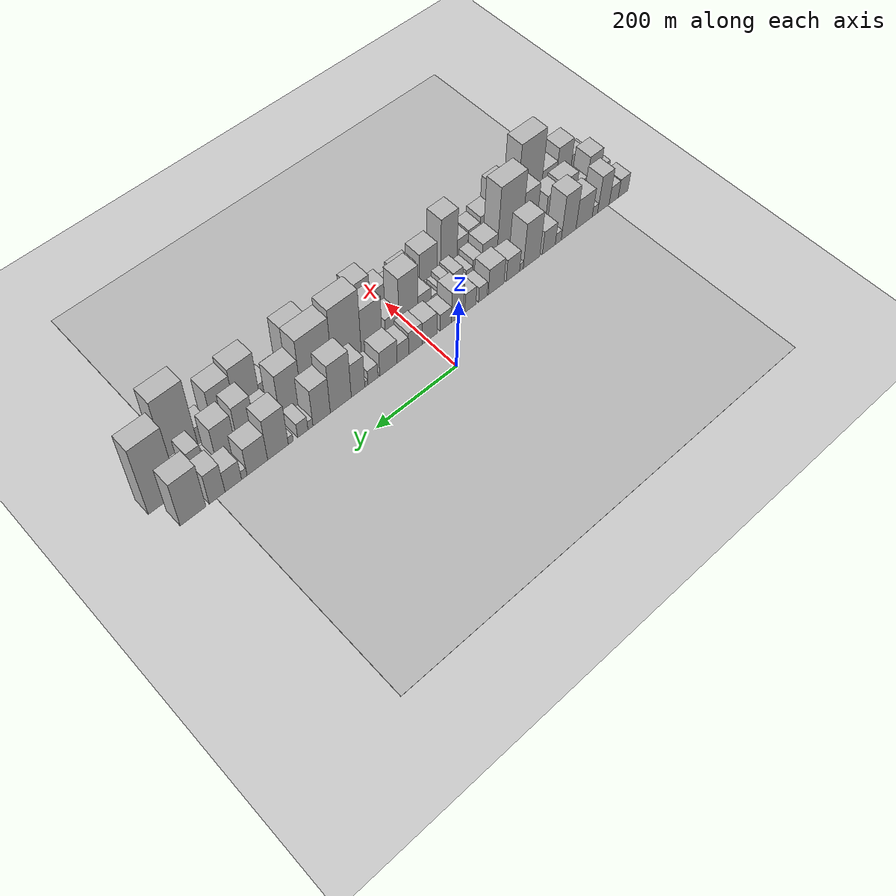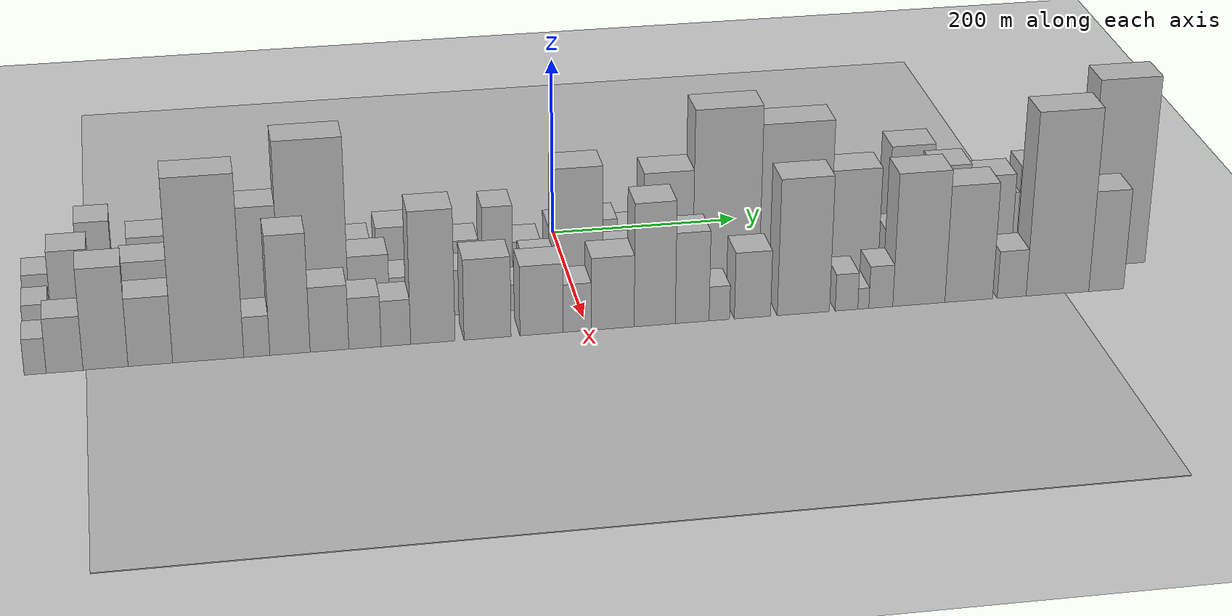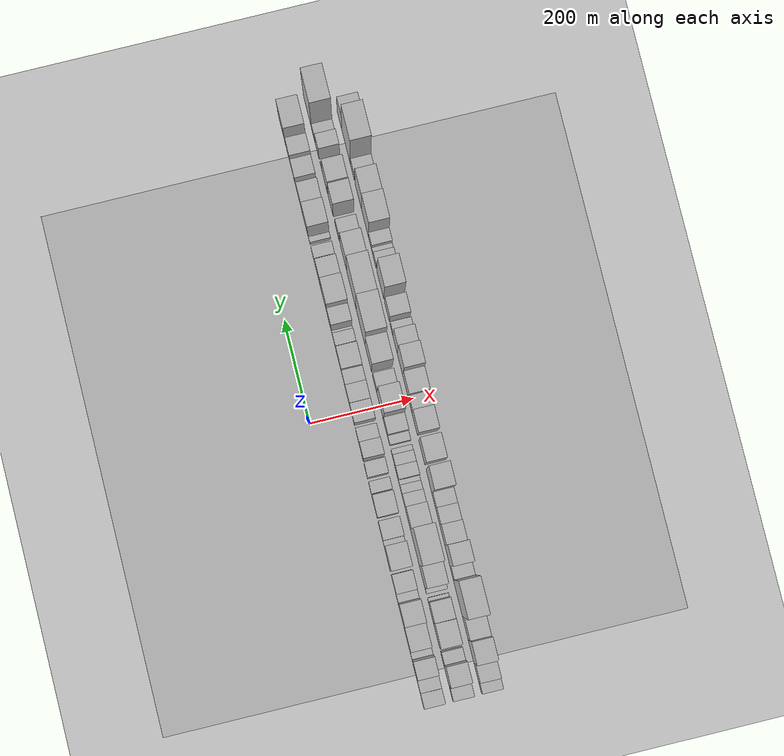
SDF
<?xml version="1.0" encoding="utf-8"?>

<sdf version="1.6">

   <world name="default">

      <gui fullscreen="0">

         <camera name="user_camera">

            <pose>-15 0 4.57585 0 0 0</pose>

            <view_controller>orbit</view_controller>

         </camera>

      </gui>

      <scene>

         <sky>

           <clouds>

             <speed>12</speed>

           </clouds>

         </sky>

         <ambient>0.4 0.4 0.4 1</ambient>

         <background>0.7 0.7 0.7 1</background>

         <shadows>1</shadows>

      </scene>

      <gravity>0 0 -9.8066</gravity>

      <magnetic_field>6e-06 2.3e-05 -4.2e-05</magnetic_field>

      <physics default="0" name="default_physics" type="ode">

         <ode>

            <solver>

               <type>quick</type>

               <iters>10</iters>

               <sor>1.0</sor>

               <use_dynamic_moi_rescaling>0</use_dynamic_moi_rescaling>

            </solver>

            <constraints>

               <cfm>0</cfm>

               <erp>0.2</erp>

               <contact_max_correcting_vel>100</contact_max_correcting_vel>

               <contact_surface_layer>0.001</contact_surface_layer>

            </constraints>

         </ode>

         <max_step_size>0.004</max_step_size>

         <real_time_factor>1</real_time_factor>

         <real_time_update_rate>250</real_time_update_rate>

      </physics>

      <light name="sun" type="directional">

         <cast_shadows>1</cast_shadows>

         <pose>0 0 10 0 0 0</pose>

         <diffuse>0.8 0.8 0.8 1</diffuse>

         <specular>0.2 0.2 0.2 1</specular>

         <attenuation>

            <range>1000</range>

            <constant>0.9</constant>

            <linear>0.01</linear>

            <quadratic>0.001</quadratic>

         </attenuation>

         <direction>-0.5 0.1 -0.9</direction>

      </light>

      <include>

         <name>ground_plane_1</name>

         <uri>model://HANNAS_ground_plane</uri>

         <pose>0 0 0  0 0 0</pose>

      </include>

      <include>

         <name>ground_plane_2</name>

         <uri>model://HANNAS_ground_plane</uri>

         <pose>100 0 0  0 0 0</pose>

      </include>

      <model name="building_1">

         <static>1</static>

         <pose frame="">100.0000 -545.5003 0 0.000000 0.000000 0.000000</pose>

         <link name="link">

            <pose frame="">0 0 27.00 0 0 0</pose>

            <collision name="collision">

               <geometry>

                  <box>

                     <size>40.0000 28.9993 54.0000</size>

                  </box>

               </geometry>

               <max_contacts>10</max_contacts>

               <surface>

                  <contact>

                     <ode/>

                  </contact>

                  <bounce/>

                  <friction>

                     <torsional>

                        <ode/>

                     </torsional>

                     <ode/>

                  </friction>

               </surface>

            </collision>

            <visual name="visual">

               <cast_shadows>0</cast_shadows>

               <geometry>

                  <box>

                     <size>40.0000 28.9993 54.0000</size>

                  </box>

               </geometry>

               <material>

                  <script>

                     <uri>model://HANNAS_wall/materials/scripts</uri>

                     <uri>model://HANNAS_wall/materials/textures</uri>

                     <name>vrc/HANNAS_wall</name>

                  </script>

               </material>

            </visual>

            <self_collide>0</self_collide>

            <enable_wind>0</enable_wind>

            <kinematic>0</kinematic>

         </link>

      </model>

      <model name="building_2">

         <static>1</static>

         <pose frame="">100.0000 -517.2635 0 0.000000 0.000000 0.000000</pose>

         <link name="link">

            <pose frame="">0 0 25.50 0 0 0</pose>

            <collision name="collision">

               <geometry>

                  <box>

                     <size>40.0000 27.4744 51.0000</size>

                  </box>

               </geometry>

               <max_contacts>10</max_contacts>

               <surface>

                  <contact>

                     <ode/>

                  </contact>

                  <bounce/>

                  <friction>

                     <torsional>

                        <ode/>

                     </torsional>

                     <ode/>

                  </friction>

               </surface>

            </collision>

            <visual name="visual">

               <cast_shadows>0</cast_shadows>

               <geometry>

                  <box>

                     <size>40.0000 27.4744 51.0000</size>

                  </box>

               </geometry>

               <material>

                  <script>

                     <uri>model://HANNAS_wall/materials/scripts</uri>

                     <uri>model://HANNAS_wall/materials/textures</uri>

                     <name>vrc/HANNAS_wall</name>

                  </script>

               </material>

            </visual>

            <self_collide>0</self_collide>

            <enable_wind>0</enable_wind>

            <kinematic>0</kinematic>

         </link>

      </model>

      <model name="building_3">

         <static>1</static>

         <pose frame="">100.0000 -486.2706 0 0.000000 0.000000 0.000000</pose>

         <link name="link">

            <pose frame="">0 0 54.00 0 0 0</pose>

            <collision name="collision">

               <geometry>

                  <box>

                     <size>40.0000 34.5114 108.0000</size>

                  </box>

               </geometry>

               <max_contacts>10</max_contacts>

               <surface>

                  <contact>

                     <ode/>

                  </contact>

                  <bounce/>

                  <friction>

                     <torsional>

                        <ode/>

                     </torsional>

                     <ode/>

                  </friction>

               </surface>

            </collision>

            <visual name="visual">

               <cast_shadows>0</cast_shadows>

               <geometry>

                  <box>

                     <size>40.0000 34.5114 108.0000</size>

                  </box>

               </geometry>

               <material>

                  <script>

                     <uri>model://HANNAS_wall/materials/scripts</uri>

                     <uri>model://HANNAS_wall/materials/textures</uri>

                     <name>vrc/HANNAS_wall</name>

                  </script>

               </material>

            </visual>

            <self_collide>0</self_collide>

            <enable_wind>0</enable_wind>

            <kinematic>0</kinematic>

         </link>

      </model>

      <model name="building_4">

         <static>1</static>

         <pose frame="">100.0000 -461.0871 0 0.000000 0.000000 0.000000</pose>

         <link name="link">

            <pose frame="">0 0 15.00 0 0 0</pose>

            <collision name="collision">

               <geometry>

                  <box>

                     <size>40.0000 15.8557 30.0000</size>

                  </box>

               </geometry>

               <max_contacts>10</max_contacts>

               <surface>

                  <contact>

                     <ode/>

                  </contact>

                  <bounce/>

                  <friction>

                     <torsional>

                        <ode/>

                     </torsional>

                     <ode/>

                  </friction>

               </surface>

            </collision>

            <visual name="visual">

               <cast_shadows>0</cast_shadows>

               <geometry>

                  <box>

                     <size>40.0000 15.8557 30.0000</size>

                  </box>

               </geometry>

               <material>

                  <script>

                     <uri>model://HANNAS_wall/materials/scripts</uri>

                     <uri>model://HANNAS_wall/materials/textures</uri>

                     <name>vrc/HANNAS_wall</name>

                  </script>

               </material>

            </visual>

            <self_collide>0</self_collide>

            <enable_wind>0</enable_wind>

            <kinematic>0</kinematic>

         </link>

      </model>

      <model name="building_5">

         <static>1</static>

         <pose frame="">100.0000 -429.2279 0 0.000000 0.000000 0.000000</pose>

         <link name="link">

            <pose frame="">0 0 43.50 0 0 0</pose>

            <collision name="collision">

               <geometry>

                  <box>

                     <size>40.0000 47.8626 87.0000</size>

                  </box>

               </geometry>

               <max_contacts>10</max_contacts>

               <surface>

                  <contact>

                     <ode/>

                  </contact>

                  <bounce/>

                  <friction>

                     <torsional>

                        <ode/>

                     </torsional>

                     <ode/>

                  </friction>

               </surface>

            </collision>

            <visual name="visual">

               <cast_shadows>0</cast_shadows>

               <geometry>

                  <box>

                     <size>40.0000 47.8626 87.0000</size>

                  </box>

               </geometry>

               <material>

                  <script>

                     <uri>model://HANNAS_wall/materials/scripts</uri>

                     <uri>model://HANNAS_wall/materials/textures</uri>

                     <name>vrc/HANNAS_wall</name>

                  </script>

               </material>

            </visual>

            <self_collide>0</self_collide>

            <enable_wind>0</enable_wind>

            <kinematic>0</kinematic>

         </link>

      </model>

      <model name="building_6">

         <static>1</static>

         <pose frame="">100.0000 -384.0020 0 0.000000 0.000000 0.000000</pose>

         <link name="link">

            <pose frame="">0 0 66.00 0 0 0</pose>

            <collision name="collision">

               <geometry>

                  <box>

                     <size>40.0000 42.5892 132.0000</size>

                  </box>

               </geometry>

               <max_contacts>10</max_contacts>

               <surface>

                  <contact>

                     <ode/>

                  </contact>

                  <bounce/>

                  <friction>

                     <torsional>

                        <ode/>

                     </torsional>

                     <ode/>

                  </friction>

               </surface>

            </collision>

            <visual name="visual">

               <cast_shadows>0</cast_shadows>

               <geometry>

                  <box>

                     <size>40.0000 42.5892 132.0000</size>

                  </box>

               </geometry>

               <material>

                  <script>

                     <uri>model://HANNAS_wall/materials/scripts</uri>

                     <uri>model://HANNAS_wall/materials/textures</uri>

                     <name>vrc/HANNAS_wall</name>

                  </script>

               </material>

            </visual>

            <self_collide>0</self_collide>

            <enable_wind>0</enable_wind>

            <kinematic>0</kinematic>

         </link>

      </model>

      <model name="building_7">

         <static>1</static>

         <pose frame="">100.0000 -354.1852 0 0.000000 0.000000 0.000000</pose>

         <link name="link">

            <pose frame="">0 0 16.50 0 0 0</pose>

            <collision name="collision">

               <geometry>

                  <box>

                     <size>40.0000 17.0444 33.0000</size>

                  </box>

               </geometry>

               <max_contacts>10</max_contacts>

               <surface>

                  <contact>

                     <ode/>

                  </contact>

                  <bounce/>

                  <friction>

                     <torsional>

                        <ode/>

                     </torsional>

                     <ode/>

                  </friction>

               </surface>

            </collision>

            <visual name="visual">

               <cast_shadows>0</cast_shadows>

               <geometry>

                  <box>

                     <size>40.0000 17.0444 33.0000</size>

                  </box>

               </geometry>

               <material>

                  <script>

                     <uri>model://HANNAS_wall/materials/scripts</uri>

                     <uri>model://HANNAS_wall/materials/textures</uri>

                     <name>vrc/HANNAS_wall</name>

                  </script>

               </material>

            </visual>

            <self_collide>0</self_collide>

            <enable_wind>0</enable_wind>

            <kinematic>0</kinematic>

         </link>

      </model>

      <model name="building_8">

         <static>1</static>

         <pose frame="">100.0000 -327.2966 0 0.000000 0.000000 0.000000</pose>

         <link name="link">

            <pose frame="">0 0 34.50 0 0 0</pose>

            <collision name="collision">

               <geometry>

                  <box>

                     <size>40.0000 36.7328 69.0000</size>

                  </box>

               </geometry>

               <max_contacts>10</max_contacts>

               <surface>

                  <contact>

                     <ode/>

                  </contact>

                  <bounce/>

                  <friction>

                     <torsional>

                        <ode/>

                     </torsional>

                     <ode/>

                  </friction>

               </surface>

            </collision>

            <visual name="visual">

               <cast_shadows>0</cast_shadows>

               <geometry>

                  <box>

                     <size>40.0000 36.7328 69.0000</size>

                  </box>

               </geometry>

               <material>

                  <script>

                     <uri>model://HANNAS_wall/materials/scripts</uri>

                     <uri>model://HANNAS_wall/materials/textures</uri>

                     <name>vrc/HANNAS_wall</name>

                  </script>

               </material>

            </visual>

            <self_collide>0</self_collide>

            <enable_wind>0</enable_wind>

            <kinematic>0</kinematic>

         </link>

      </model>

      <model name="building_9">

         <static>1</static>

         <pose frame="">100.0000 -278.6413 0 0.000000 0.000000 0.000000</pose>

         <link name="link">

            <pose frame="">0 0 67.50 0 0 0</pose>

            <collision name="collision">

               <geometry>

                  <box>

                     <size>40.0000 46.5779 135.0000</size>

                  </box>

               </geometry>

               <max_contacts>10</max_contacts>

               <surface>

                  <contact>

                     <ode/>

                  </contact>

                  <bounce/>

                  <friction>

                     <torsional>

                        <ode/>

                     </torsional>

                     <ode/>

                  </friction>

               </surface>

            </collision>

            <visual name="visual">

               <cast_shadows>0</cast_shadows>

               <geometry>

                  <box>

                     <size>40.0000 46.5779 135.0000</size>

                  </box>

               </geometry>

               <material>

                  <script>

                     <uri>model://HANNAS_wall/materials/scripts</uri>

                     <uri>model://HANNAS_wall/materials/textures</uri>

                     <name>vrc/HANNAS_wall</name>

                  </script>

               </material>

            </visual>

            <self_collide>0</self_collide>

            <enable_wind>0</enable_wind>

            <kinematic>0</kinematic>

         </link>

      </model>

      <model name="building_10">

         <static>1</static>

         <pose frame="">100.0000 -250.1862 0 0.000000 0.000000 0.000000</pose>

         <link name="link">

            <pose frame="">0 0 12.00 0 0 0</pose>

            <collision name="collision">

               <geometry>

                  <box>

                     <size>40.0000 10.3321 24.0000</size>

                  </box>

               </geometry>

               <max_contacts>10</max_contacts>

               <surface>

                  <contact>

                     <ode/>

                  </contact>

                  <bounce/>

                  <friction>

                     <torsional>

                        <ode/>

                     </torsional>

                     <ode/>

                  </friction>

               </surface>

            </collision>

            <visual name="visual">

               <cast_shadows>0</cast_shadows>

               <geometry>

                  <box>

                     <size>40.0000 10.3321 24.0000</size>

                  </box>

               </geometry>

               <material>

                  <script>

                     <uri>model://HANNAS_wall/materials/scripts</uri>

                     <uri>model://HANNAS_wall/materials/textures</uri>

                     <name>vrc/HANNAS_wall</name>

                  </script>

               </material>

            </visual>

            <self_collide>0</self_collide>

            <enable_wind>0</enable_wind>

            <kinematic>0</kinematic>

         </link>

      </model>

      <model name="building_11">

         <static>1</static>

         <pose frame="">100.0000 -226.5578 0 0.000000 0.000000 0.000000</pose>

         <link name="link">

            <pose frame="">0 0 33.00 0 0 0</pose>

            <collision name="collision">

               <geometry>

                  <box>

                     <size>40.0000 36.9247 66.0000</size>

                  </box>

               </geometry>

               <max_contacts>10</max_contacts>

               <surface>

                  <contact>

                     <ode/>

                  </contact>

                  <bounce/>

                  <friction>

                     <torsional>

                        <ode/>

                     </torsional>

                     <ode/>

                  </friction>

               </surface>

            </collision>

            <visual name="visual">

               <cast_shadows>0</cast_shadows>

               <geometry>

                  <box>

                     <size>40.0000 36.9247 66.0000</size>

                  </box>

               </geometry>

               <material>

                  <script>

                     <uri>model://HANNAS_wall/materials/scripts</uri>

                     <uri>model://HANNAS_wall/materials/textures</uri>

                     <name>vrc/HANNAS_wall</name>

                  </script>

               </material>

            </visual>

            <self_collide>0</self_collide>

            <enable_wind>0</enable_wind>

            <kinematic>0</kinematic>

         </link>

      </model>

      <model name="building_12">

         <static>1</static>

         <pose frame="">100.0000 -180.7119 0 0.000000 0.000000 0.000000</pose>

         <link name="link">

            <pose frame="">0 0 39.00 0 0 0</pose>

            <collision name="collision">

               <geometry>

                  <box>

                     <size>40.0000 42.7672 78.0000</size>

                  </box>

               </geometry>

               <max_contacts>10</max_contacts>

               <surface>

                  <contact>

                     <ode/>

                  </contact>

                  <bounce/>

                  <friction>

                     <torsional>

                        <ode/>

                     </torsional>

                     <ode/>

                  </friction>

               </surface>

            </collision>

            <visual name="visual">

               <cast_shadows>0</cast_shadows>

               <geometry>

                  <box>

                     <size>40.0000 42.7672 78.0000</size>

                  </box>

               </geometry>

               <material>

                  <script>

                     <uri>model://HANNAS_wall/materials/scripts</uri>

                     <uri>model://HANNAS_wall/materials/textures</uri>

                     <name>vrc/HANNAS_wall</name>

                  </script>

               </material>

            </visual>

            <self_collide>0</self_collide>

            <enable_wind>0</enable_wind>

            <kinematic>0</kinematic>

         </link>

      </model>

      <model name="building_13">

         <static>1</static>

         <pose frame="">100.0000 -144.7670 0 0.000000 0.000000 0.000000</pose>

         <link name="link">

            <pose frame="">0 0 22.50 0 0 0</pose>

            <collision name="collision">

               <geometry>

                  <box>

                     <size>40.0000 23.1226 45.0000</size>

                  </box>

               </geometry>

               <max_contacts>10</max_contacts>

               <surface>

                  <contact>

                     <ode/>

                  </contact>

                  <bounce/>

                  <friction>

                     <torsional>

                        <ode/>

                     </torsional>

                     <ode/>

                  </friction>

               </surface>

            </collision>

            <visual name="visual">

               <cast_shadows>0</cast_shadows>

               <geometry>

                  <box>

                     <size>40.0000 23.1226 45.0000</size>

                  </box>

               </geometry>

               <material>

                  <script>

                     <uri>model://HANNAS_wall/materials/scripts</uri>

                     <uri>model://HANNAS_wall/materials/textures</uri>

                     <name>vrc/HANNAS_wall</name>

                  </script>

               </material>

            </visual>

            <self_collide>0</self_collide>

            <enable_wind>0</enable_wind>

            <kinematic>0</kinematic>

         </link>

      </model>

      <model name="building_14">

         <static>1</static>

         <pose frame="">100.0000 -111.3306 0 0.000000 0.000000 0.000000</pose>

         <link name="link">

            <pose frame="">0 0 28.50 0 0 0</pose>

            <collision name="collision">

               <geometry>

                  <box>

                     <size>40.0000 29.7501 57.0000</size>

                  </box>

               </geometry>

               <max_contacts>10</max_contacts>

               <surface>

                  <contact>

                     <ode/>

                  </contact>

                  <bounce/>

                  <friction>

                     <torsional>

                        <ode/>

                     </torsional>

                     <ode/>

                  </friction>

               </surface>

            </collision>

            <visual name="visual">

               <cast_shadows>0</cast_shadows>

               <geometry>

                  <box>

                     <size>40.0000 29.7501 57.0000</size>

                  </box>

               </geometry>

               <material>

                  <script>

                     <uri>model://HANNAS_wall/materials/scripts</uri>

                     <uri>model://HANNAS_wall/materials/textures</uri>

                     <name>vrc/HANNAS_wall</name>

                  </script>

               </material>

            </visual>

            <self_collide>0</self_collide>

            <enable_wind>0</enable_wind>

            <kinematic>0</kinematic>

         </link>

      </model>

      <model name="building_15">

         <static>1</static>

         <pose frame="">100.0000 -76.7098 0 0.000000 0.000000 0.000000</pose>

         <link name="link">

            <pose frame="">0 0 46.50 0 0 0</pose>

            <collision name="collision">

               <geometry>

                  <box>

                     <size>40.0000 31.4915 93.0000</size>

                  </box>

               </geometry>

               <max_contacts>10</max_contacts>

               <surface>

                  <contact>

                     <ode/>

                  </contact>

                  <bounce/>

                  <friction>

                     <torsional>

                        <ode/>

                     </torsional>

                     <ode/>

                  </friction>

               </surface>

            </collision>

            <visual name="visual">

               <cast_shadows>0</cast_shadows>

               <geometry>

                  <box>

                     <size>40.0000 31.4915 93.0000</size>

                  </box>

               </geometry>

               <material>

                  <script>

                     <uri>model://HANNAS_wall/materials/scripts</uri>

                     <uri>model://HANNAS_wall/materials/textures</uri>

                     <name>vrc/HANNAS_wall</name>

                  </script>

               </material>

            </visual>

            <self_collide>0</self_collide>

            <enable_wind>0</enable_wind>

            <kinematic>0</kinematic>

         </link>

      </model>

      <model name="building_16">

         <static>1</static>

         <pose frame="">100.0000 -46.2156 0 0.000000 0.000000 0.000000</pose>

         <link name="link">

            <pose frame="">0 0 25.50 0 0 0</pose>

            <collision name="collision">

               <geometry>

                  <box>

                     <size>40.0000 29.4970 51.0000</size>

                  </box>

               </geometry>

               <max_contacts>10</max_contacts>

               <surface>

                  <contact>

                     <ode/>

                  </contact>

                  <bounce/>

                  <friction>

                     <torsional>

                        <ode/>

                     </torsional>

                     <ode/>

                  </friction>

               </surface>

            </collision>

            <visual name="visual">

               <cast_shadows>0</cast_shadows>

               <geometry>

                  <box>

                     <size>40.0000 29.4970 51.0000</size>

                  </box>

               </geometry>

               <material>

                  <script>

                     <uri>model://HANNAS_wall/materials/scripts</uri>

                     <uri>model://HANNAS_wall/materials/textures</uri>

                     <name>vrc/HANNAS_wall</name>

                  </script>

               </material>

            </visual>

            <self_collide>0</self_collide>

            <enable_wind>0</enable_wind>

            <kinematic>0</kinematic>

         </link>

      </model>

      <model name="building_17">

         <static>1</static>

         <pose frame="">100.0000 -4.5980 0 0.000000 0.000000 0.000000</pose>

         <link name="link">

            <pose frame="">0 0 33.00 0 0 0</pose>

            <collision name="collision">

               <geometry>

                  <box>

                     <size>40.0000 37.7381 66.0000</size>

                  </box>

               </geometry>

               <max_contacts>10</max_contacts>

               <surface>

                  <contact>

                     <ode/>

                  </contact>

                  <bounce/>

                  <friction>

                     <torsional>

                        <ode/>

                     </torsional>

                     <ode/>

                  </friction>

               </surface>

            </collision>

            <visual name="visual">

               <cast_shadows>0</cast_shadows>

               <geometry>

                  <box>

                     <size>40.0000 37.7381 66.0000</size>

                  </box>

               </geometry>

               <material>

                  <script>

                     <uri>model://HANNAS_wall/materials/scripts</uri>

                     <uri>model://HANNAS_wall/materials/textures</uri>

                     <name>vrc/HANNAS_wall</name>

                  </script>

               </material>

            </visual>

            <self_collide>0</self_collide>

            <enable_wind>0</enable_wind>

            <kinematic>0</kinematic>

         </link>

      </model>

      <model name="building_18">

         <static>1</static>

         <pose frame="">100.0000 31.6166 0 0.000000 0.000000 0.000000</pose>

         <link name="link">

            <pose frame="">0 0 34.50 0 0 0</pose>

            <collision name="collision">

               <geometry>

                  <box>

                     <size>40.0000 34.6912 69.0000</size>

                  </box>

               </geometry>

               <max_contacts>10</max_contacts>

               <surface>

                  <contact>

                     <ode/>

                  </contact>

                  <bounce/>

                  <friction>

                     <torsional>

                        <ode/>

                     </torsional>

                     <ode/>

                  </friction>

               </surface>

            </collision>

            <visual name="visual">

               <cast_shadows>0</cast_shadows>

               <geometry>

                  <box>

                     <size>40.0000 34.6912 69.0000</size>

                  </box>

               </geometry>

               <material>

                  <script>

                     <uri>model://HANNAS_wall/materials/scripts</uri>

                     <uri>model://HANNAS_wall/materials/textures</uri>

                     <name>vrc/HANNAS_wall</name>

                  </script>

               </material>

            </visual>

            <self_collide>0</self_collide>

            <enable_wind>0</enable_wind>

            <kinematic>0</kinematic>

         </link>

      </model>

      <model name="building_19">

         <static>1</static>

         <pose frame="">100.0000 63.4037 0 0.000000 0.000000 0.000000</pose>

         <link name="link">

            <pose frame="">0 0 28.50 0 0 0</pose>

            <collision name="collision">

               <geometry>

                  <box>

                     <size>40.0000 28.8829 57.0000</size>

                  </box>

               </geometry>

               <max_contacts>10</max_contacts>

               <surface>

                  <contact>

                     <ode/>

                  </contact>

                  <bounce/>

                  <friction>

                     <torsional>

                        <ode/>

                     </torsional>

                     <ode/>

                  </friction>

               </surface>

            </collision>

            <visual name="visual">

               <cast_shadows>0</cast_shadows>

               <geometry>

                  <box>

                     <size>40.0000 28.8829 57.0000</size>

                  </box>

               </geometry>

               <material>

                  <script>

                     <uri>model://HANNAS_wall/materials/scripts</uri>

                     <uri>model://HANNAS_wall/materials/textures</uri>

                     <name>vrc/HANNAS_wall</name>

                  </script>

               </material>

            </visual>

            <self_collide>0</self_collide>

            <enable_wind>0</enable_wind>

            <kinematic>0</kinematic>

         </link>

      </model>

      <model name="building_20">

         <static>1</static>

         <pose frame="">100.0000 99.6497 0 0.000000 0.000000 0.000000</pose>

         <link name="link">

            <pose frame="">0 0 37.50 0 0 0</pose>

            <collision name="collision">

               <geometry>

                  <box>

                     <size>40.0000 43.6092 75.0000</size>

                  </box>

               </geometry>

               <max_contacts>10</max_contacts>

               <surface>

                  <contact>

                     <ode/>

                  </contact>

                  <bounce/>

                  <friction>

                     <torsional>

                        <ode/>

                     </torsional>

                     <ode/>

                  </friction>

               </surface>

            </collision>

            <visual name="visual">

               <cast_shadows>0</cast_shadows>

               <geometry>

                  <box>

                     <size>40.0000 43.6092 75.0000</size>

                  </box>

               </geometry>

               <material>

                  <script>

                     <uri>model://HANNAS_wall/materials/scripts</uri>

                     <uri>model://HANNAS_wall/materials/textures</uri>

                     <name>vrc/HANNAS_wall</name>

                  </script>

               </material>

            </visual>

            <self_collide>0</self_collide>

            <enable_wind>0</enable_wind>

            <kinematic>0</kinematic>

         </link>

      </model>

      <model name="building_21">

         <static>1</static>

         <pose frame="">100.0000 137.8043 0 0.000000 0.000000 0.000000</pose>

         <link name="link">

            <pose frame="">0 0 22.50 0 0 0</pose>

            <collision name="collision">

               <geometry>

                  <box>

                     <size>40.0000 24.7000 45.0000</size>

                  </box>

               </geometry>

               <max_contacts>10</max_contacts>

               <surface>

                  <contact>

                     <ode/>

                  </contact>

                  <bounce/>

                  <friction>

                     <torsional>

                        <ode/>

                     </torsional>

                     <ode/>

                  </friction>

               </surface>

            </collision>

            <visual name="visual">

               <cast_shadows>0</cast_shadows>

               <geometry>

                  <box>

                     <size>40.0000 24.7000 45.0000</size>

                  </box>

               </geometry>

               <material>

                  <script>

                     <uri>model://HANNAS_wall/materials/scripts</uri>

                     <uri>model://HANNAS_wall/materials/textures</uri>

                     <name>vrc/HANNAS_wall</name>

                  </script>

               </material>

            </visual>

            <self_collide>0</self_collide>

            <enable_wind>0</enable_wind>

            <kinematic>0</kinematic>

         </link>

      </model>

      <model name="building_22">

         <static>1</static>

         <pose frame="">100.0000 154.0484 0 0.000000 0.000000 0.000000</pose>

         <link name="link">

            <pose frame="">0 0 9.00 0 0 0</pose>

            <collision name="collision">

               <geometry>

                  <box>

                     <size>40.0000 7.7882 18.0000</size>

                  </box>

               </geometry>

               <max_contacts>10</max_contacts>

               <surface>

                  <contact>

                     <ode/>

                  </contact>

                  <bounce/>

                  <friction>

                     <torsional>

                        <ode/>

                     </torsional>

                     <ode/>

                  </friction>

               </surface>

            </collision>

            <visual name="visual">

               <cast_shadows>0</cast_shadows>

               <geometry>

                  <box>

                     <size>40.0000 7.7882 18.0000</size>

                  </box>

               </geometry>

               <material>

                  <script>

                     <uri>model://HANNAS_wall/materials/scripts</uri>

                     <uri>model://HANNAS_wall/materials/textures</uri>

                     <name>vrc/HANNAS_wall</name>

                  </script>

               </material>

            </visual>

            <self_collide>0</self_collide>

            <enable_wind>0</enable_wind>

            <kinematic>0</kinematic>

         </link>

      </model>

      <model name="building_23">

         <static>1</static>

         <pose frame="">100.0000 174.3173 0 0.000000 0.000000 0.000000</pose>

         <link name="link">

            <pose frame="">0 0 51.00 0 0 0</pose>

            <collision name="collision">

               <geometry>

                  <box>

                     <size>40.0000 32.7497 102.0000</size>

                  </box>

               </geometry>

               <max_contacts>10</max_contacts>

               <surface>

                  <contact>

                     <ode/>

                  </contact>

                  <bounce/>

                  <friction>

                     <torsional>

                        <ode/>

                     </torsional>

                     <ode/>

                  </friction>

               </surface>

            </collision>

            <visual name="visual">

               <cast_shadows>0</cast_shadows>

               <geometry>

                  <box>

                     <size>40.0000 32.7497 102.0000</size>

                  </box>

               </geometry>

               <material>

                  <script>

                     <uri>model://HANNAS_wall/materials/scripts</uri>

                     <uri>model://HANNAS_wall/materials/textures</uri>

                     <name>vrc/HANNAS_wall</name>

                  </script>

               </material>

            </visual>

            <self_collide>0</self_collide>

            <enable_wind>0</enable_wind>

            <kinematic>0</kinematic>

         </link>

      </model>

      <model name="building_24">

         <static>1</static>

         <pose frame="">100.0000 215.7689 0 0.000000 0.000000 0.000000</pose>

         <link name="link">

            <pose frame="">0 0 75.00 0 0 0</pose>

            <collision name="collision">

               <geometry>

                  <box>

                     <size>40.0000 50.1534 150.0000</size>

                  </box>

               </geometry>

               <max_contacts>10</max_contacts>

               <surface>

                  <contact>

                     <ode/>

                  </contact>

                  <bounce/>

                  <friction>

                     <torsional>

                        <ode/>

                     </torsional>

                     <ode/>

                  </friction>

               </surface>

            </collision>

            <visual name="visual">

               <cast_shadows>0</cast_shadows>

               <geometry>

                  <box>

                     <size>40.0000 50.1534 150.0000</size>

                  </box>

               </geometry>

               <material>

                  <script>

                     <uri>model://HANNAS_wall/materials/scripts</uri>

                     <uri>model://HANNAS_wall/materials/textures</uri>

                     <name>vrc/HANNAS_wall</name>

                  </script>

               </material>

            </visual>

            <self_collide>0</self_collide>

            <enable_wind>0</enable_wind>

            <kinematic>0</kinematic>

         </link>

      </model>

      <model name="building_25">

         <static>1</static>

         <pose frame="">100.0000 261.4154 0 0.000000 0.000000 0.000000</pose>

         <link name="link">

            <pose frame="">0 0 57.00 0 0 0</pose>

            <collision name="collision">

               <geometry>

                  <box>

                     <size>40.0000 41.1397 114.0000</size>

                  </box>

               </geometry>

               <max_contacts>10</max_contacts>

               <surface>

                  <contact>

                     <ode/>

                  </contact>

                  <bounce/>

                  <friction>

                     <torsional>

                        <ode/>

                     </torsional>

                     <ode/>

                  </friction>

               </surface>

            </collision>

            <visual name="visual">

               <cast_shadows>0</cast_shadows>

               <geometry>

                  <box>

                     <size>40.0000 41.1397 114.0000</size>

                  </box>

               </geometry>

               <material>

                  <script>

                     <uri>model://HANNAS_wall/materials/scripts</uri>

                     <uri>model://HANNAS_wall/materials/textures</uri>

                     <name>vrc/HANNAS_wall</name>

                  </script>

               </material>

            </visual>

            <self_collide>0</self_collide>

            <enable_wind>0</enable_wind>

            <kinematic>0</kinematic>

         </link>

      </model>

      <model name="building_26">

         <static>1</static>

         <pose frame="">100.0000 287.8555 0 0.000000 0.000000 0.000000</pose>

         <link name="link">

            <pose frame="">0 0 13.50 0 0 0</pose>

            <collision name="collision">

               <geometry>

                  <box>

                     <size>40.0000 11.7404 27.0000</size>

                  </box>

               </geometry>

               <max_contacts>10</max_contacts>

               <surface>

                  <contact>

                     <ode/>

                  </contact>

                  <bounce/>

                  <friction>

                     <torsional>

                        <ode/>

                     </torsional>

                     <ode/>

                  </friction>

               </surface>

            </collision>

            <visual name="visual">

               <cast_shadows>0</cast_shadows>

               <geometry>

                  <box>

                     <size>40.0000 11.7404 27.0000</size>

                  </box>

               </geometry>

               <material>

                  <script>

                     <uri>model://HANNAS_wall/materials/scripts</uri>

                     <uri>model://HANNAS_wall/materials/textures</uri>

                     <name>vrc/HANNAS_wall</name>

                  </script>

               </material>

            </visual>

            <self_collide>0</self_collide>

            <enable_wind>0</enable_wind>

            <kinematic>0</kinematic>

         </link>

      </model>

      <model name="building_27">

         <static>1</static>

         <pose frame="">100.0000 305.8213 0 0.000000 0.000000 0.000000</pose>

         <link name="link">

            <pose frame="">0 0 22.50 0 0 0</pose>

            <collision name="collision">

               <geometry>

                  <box>

                     <size>40.0000 24.1912 45.0000</size>

                  </box>

               </geometry>

               <max_contacts>10</max_contacts>

               <surface>

                  <contact>

                     <ode/>

                  </contact>

                  <bounce/>

                  <friction>

                     <torsional>

                        <ode/>

                     </torsional>

                     <ode/>

                  </friction>

               </surface>

            </collision>

            <visual name="visual">

               <cast_shadows>0</cast_shadows>

               <geometry>

                  <box>

                     <size>40.0000 24.1912 45.0000</size>

                  </box>

               </geometry>

               <material>

                  <script>

                     <uri>model://HANNAS_wall/materials/scripts</uri>

                     <uri>model://HANNAS_wall/materials/textures</uri>

                     <name>vrc/HANNAS_wall</name>

                  </script>

               </material>

            </visual>

            <self_collide>0</self_collide>

            <enable_wind>0</enable_wind>

            <kinematic>0</kinematic>

         </link>

      </model>

      <model name="building_28">

         <static>1</static>

         <pose frame="">100.0000 333.5547 0 0.000000 0.000000 0.000000</pose>

         <link name="link">

            <pose frame="">0 0 12.00 0 0 0</pose>

            <collision name="collision">

               <geometry>

                  <box>

                     <size>40.0000 11.2756 24.0000</size>

                  </box>

               </geometry>

               <max_contacts>10</max_contacts>

               <surface>

                  <contact>

                     <ode/>

                  </contact>

                  <bounce/>

                  <friction>

                     <torsional>

                        <ode/>

                     </torsional>

                     <ode/>

                  </friction>

               </surface>

            </collision>

            <visual name="visual">

               <cast_shadows>0</cast_shadows>

               <geometry>

                  <box>

                     <size>40.0000 11.2756 24.0000</size>

                  </box>

               </geometry>

               <material>

                  <script>

                     <uri>model://HANNAS_wall/materials/scripts</uri>

                     <uri>model://HANNAS_wall/materials/textures</uri>

                     <name>vrc/HANNAS_wall</name>

                  </script>

               </material>

            </visual>

            <self_collide>0</self_collide>

            <enable_wind>0</enable_wind>

            <kinematic>0</kinematic>

         </link>

      </model>

      <model name="building_29">

         <static>1</static>

         <pose frame="">100.0000 362.8317 0 0.000000 0.000000 0.000000</pose>

         <link name="link">

            <pose frame="">0 0 64.50 0 0 0</pose>

            <collision name="collision">

               <geometry>

                  <box>

                     <size>40.0000 47.2785 129.0000</size>

                  </box>

               </geometry>

               <max_contacts>10</max_contacts>

               <surface>

                  <contact>

                     <ode/>

                  </contact>

                  <bounce/>

                  <friction>

                     <torsional>

                        <ode/>

                     </torsional>

                     <ode/>

                  </friction>

               </surface>

            </collision>

            <visual name="visual">

               <cast_shadows>0</cast_shadows>

               <geometry>

                  <box>

                     <size>40.0000 47.2785 129.0000</size>

                  </box>

               </geometry>

               <material>

                  <script>

                     <uri>model://HANNAS_wall/materials/scripts</uri>

                     <uri>model://HANNAS_wall/materials/textures</uri>

                     <name>vrc/HANNAS_wall</name>

                  </script>

               </material>

            </visual>

            <self_collide>0</self_collide>

            <enable_wind>0</enable_wind>

            <kinematic>0</kinematic>

         </link>

      </model>

      <model name="building_30">

         <static>1</static>

         <pose frame="">100.0000 409.5287 0 0.000000 0.000000 0.000000</pose>

         <link name="link">

            <pose frame="">0 0 43.50 0 0 0</pose>

            <collision name="collision">

               <geometry>

                  <box>

                     <size>40.0000 46.1154 87.0000</size>

                  </box>

               </geometry>

               <max_contacts>10</max_contacts>

               <surface>

                  <contact>

                     <ode/>

                  </contact>

                  <bounce/>

                  <friction>

                     <torsional>

                        <ode/>

                     </torsional>

                     <ode/>

                  </friction>

               </surface>

            </collision>

            <visual name="visual">

               <cast_shadows>0</cast_shadows>

               <geometry>

                  <box>

                     <size>40.0000 46.1154 87.0000</size>

                  </box>

               </geometry>

               <material>

                  <script>

                     <uri>model://HANNAS_wall/materials/scripts</uri>

                     <uri>model://HANNAS_wall/materials/textures</uri>

                     <name>vrc/HANNAS_wall</name>

                  </script>

               </material>

            </visual>

            <self_collide>0</self_collide>

            <enable_wind>0</enable_wind>

            <kinematic>0</kinematic>

         </link>

      </model>

      <model name="building_31">

         <static>1</static>

         <pose frame="">100.0000 438.7715 0 0.000000 0.000000 0.000000</pose>

         <link name="link">

            <pose frame="">0 0 13.50 0 0 0</pose>

            <collision name="collision">

               <geometry>

                  <box>

                     <size>40.0000 12.3703 27.0000</size>

                  </box>

               </geometry>

               <max_contacts>10</max_contacts>

               <surface>

                  <contact>

                     <ode/>

                  </contact>

                  <bounce/>

                  <friction>

                     <torsional>

                        <ode/>

                     </torsional>

                     <ode/>

                  </friction>

               </surface>

            </collision>

            <visual name="visual">

               <cast_shadows>0</cast_shadows>

               <geometry>

                  <box>

                     <size>40.0000 12.3703 27.0000</size>

                  </box>

               </geometry>

               <material>

                  <script>

                     <uri>model://HANNAS_wall/materials/scripts</uri>

                     <uri>model://HANNAS_wall/materials/textures</uri>

                     <name>vrc/HANNAS_wall</name>

                  </script>

               </material>

            </visual>

            <self_collide>0</self_collide>

            <enable_wind>0</enable_wind>

            <kinematic>0</kinematic>

         </link>

      </model>

      <model name="building_32">

         <static>1</static>

         <pose frame="">100.0000 463.2627 0 0.000000 0.000000 0.000000</pose>

         <link name="link">

            <pose frame="">0 0 33.00 0 0 0</pose>

            <collision name="collision">

               <geometry>

                  <box>

                     <size>40.0000 36.6119 66.0000</size>

                  </box>

               </geometry>

               <max_contacts>10</max_contacts>

               <surface>

                  <contact>

                     <ode/>

                  </contact>

                  <bounce/>

                  <friction>

                     <torsional>

                        <ode/>

                     </torsional>

                     <ode/>

                  </friction>

               </surface>

            </collision>

            <visual name="visual">

               <cast_shadows>0</cast_shadows>

               <geometry>

                  <box>

                     <size>40.0000 36.6119 66.0000</size>

                  </box>

               </geometry>

               <material>

                  <script>

                     <uri>model://HANNAS_wall/materials/scripts</uri>

                     <uri>model://HANNAS_wall/materials/textures</uri>

                     <name>vrc/HANNAS_wall</name>

                  </script>

               </material>

            </visual>

            <self_collide>0</self_collide>

            <enable_wind>0</enable_wind>

            <kinematic>0</kinematic>

         </link>

      </model>

      <model name="building_33">

         <static>1</static>

         <pose frame="">100.0000 498.8720 0 0.000000 0.000000 0.000000</pose>

         <link name="link">

            <pose frame="">0 0 48.00 0 0 0</pose>

            <collision name="collision">

               <geometry>

                  <box>

                     <size>40.0000 34.6068 96.0000</size>

                  </box>

               </geometry>

               <max_contacts>10</max_contacts>

               <surface>

                  <contact>

                     <ode/>

                  </contact>

                  <bounce/>

                  <friction>

                     <torsional>

                        <ode/>

                     </torsional>

                     <ode/>

                  </friction>

               </surface>

            </collision>

            <visual name="visual">

               <cast_shadows>0</cast_shadows>

               <geometry>

                  <box>

                     <size>40.0000 34.6068 96.0000</size>

                  </box>

               </geometry>

               <material>

                  <script>

                     <uri>model://HANNAS_wall/materials/scripts</uri>

                     <uri>model://HANNAS_wall/materials/textures</uri>

                     <name>vrc/HANNAS_wall</name>

                  </script>

               </material>

            </visual>

            <self_collide>0</self_collide>

            <enable_wind>0</enable_wind>

            <kinematic>0</kinematic>

         </link>

      </model>

      <model name="building_34">

         <static>1</static>

         <pose frame="">100.0000 550.8680 0 0.000000 0.000000 0.000000</pose>

         <link name="link">

            <pose frame="">0 0 70.50 0 0 0</pose>

            <collision name="collision">

               <geometry>

                  <box>

                     <size>40.0000 55.3852 141.0000</size>

                  </box>

               </geometry>

               <max_contacts>10</max_contacts>

               <surface>

                  <contact>

                     <ode/>

                  </contact>

                  <bounce/>

                  <friction>

                     <torsional>

                        <ode/>

                     </torsional>

                     <ode/>

                  </friction>

               </surface>

            </collision>

            <visual name="visual">

               <cast_shadows>0</cast_shadows>

               <geometry>

                  <box>

                     <size>40.0000 55.3852 141.0000</size>

                  </box>

               </geometry>

               <material>

                  <script>

                     <uri>model://HANNAS_wall/materials/scripts</uri>

                     <uri>model://HANNAS_wall/materials/textures</uri>

                     <name>vrc/HANNAS_wall</name>

                  </script>

               </material>

            </visual>

            <self_collide>0</self_collide>

            <enable_wind>0</enable_wind>

            <kinematic>0</kinematic>

         </link>

      </model>

      <model name="building_35">

         <static>1</static>

         <pose frame="">155.0000 -547.1190 0 0.000000 0.000000 0.000000</pose>

         <link name="link">

            <pose frame="">0 0 24.00 0 0 0</pose>

            <collision name="collision">

               <geometry>

                  <box>

                     <size>40.0000 25.7619 48.0000</size>

                  </box>

               </geometry>

               <max_contacts>10</max_contacts>

               <surface>

                  <contact>

                     <ode/>

                  </contact>

                  <bounce/>

                  <friction>

                     <torsional>

                        <ode/>

                     </torsional>

                     <ode/>

                  </friction>

               </surface>

            </collision>

            <visual name="visual">

               <cast_shadows>0</cast_shadows>

               <geometry>

                  <box>

                     <size>40.0000 25.7619 48.0000</size>

                  </box>

               </geometry>

               <material>

                  <script>

                     <uri>model://HANNAS_wall/materials/scripts</uri>

                     <uri>model://HANNAS_wall/materials/textures</uri>

                     <name>vrc/HANNAS_wall</name>

                  </script>

               </material>

            </visual>

            <self_collide>0</self_collide>

            <enable_wind>0</enable_wind>

            <kinematic>0</kinematic>

         </link>

      </model>

      <model name="building_36">

         <static>1</static>

         <pose frame="">155.0000 -511.6188 0 0.000000 0.000000 0.000000</pose>

         <link name="link">

            <pose frame="">0 0 52.50 0 0 0</pose>

            <collision name="collision">

               <geometry>

                  <box>

                     <size>40.0000 39.2385 105.0000</size>

                  </box>

               </geometry>

               <max_contacts>10</max_contacts>

               <surface>

                  <contact>

                     <ode/>

                  </contact>

                  <bounce/>

                  <friction>

                     <torsional>

                        <ode/>

                     </torsional>

                     <ode/>

                  </friction>

               </surface>

            </collision>

            <visual name="visual">

               <cast_shadows>0</cast_shadows>

               <geometry>

                  <box>

                     <size>40.0000 39.2385 105.0000</size>

                  </box>

               </geometry>

               <material>

                  <script>

                     <uri>model://HANNAS_wall/materials/scripts</uri>

                     <uri>model://HANNAS_wall/materials/textures</uri>

                     <name>vrc/HANNAS_wall</name>

                  </script>

               </material>

            </visual>

            <self_collide>0</self_collide>

            <enable_wind>0</enable_wind>

            <kinematic>0</kinematic>

         </link>

      </model>

      <model name="building_37">

         <static>1</static>

         <pose frame="">155.0000 -479.9072 0 0.000000 0.000000 0.000000</pose>

         <link name="link">

            <pose frame="">0 0 24.00 0 0 0</pose>

            <collision name="collision">

               <geometry>

                  <box>

                     <size>40.0000 24.1847 48.0000</size>

                  </box>

               </geometry>

               <max_contacts>10</max_contacts>

               <surface>

                  <contact>

                     <ode/>

                  </contact>

                  <bounce/>

                  <friction>

                     <torsional>

                        <ode/>

                     </torsional>

                     <ode/>

                  </friction>

               </surface>

            </collision>

            <visual name="visual">

               <cast_shadows>0</cast_shadows>

               <geometry>

                  <box>

                     <size>40.0000 24.1847 48.0000</size>

                  </box>

               </geometry>

               <material>

                  <script>

                     <uri>model://HANNAS_wall/materials/scripts</uri>

                     <uri>model://HANNAS_wall/materials/textures</uri>

                     <name>vrc/HANNAS_wall</name>

                  </script>

               </material>

            </visual>

            <self_collide>0</self_collide>

            <enable_wind>0</enable_wind>

            <kinematic>0</kinematic>

         </link>

      </model>

      <model name="building_38">

         <static>1</static>

         <pose frame="">155.0000 -436.9973 0 0.000000 0.000000 0.000000</pose>

         <link name="link">

            <pose frame="">0 0 43.50 0 0 0</pose>

            <collision name="collision">

               <geometry>

                  <box>

                     <size>40.0000 47.6350 87.0000</size>

                  </box>

               </geometry>

               <max_contacts>10</max_contacts>

               <surface>

                  <contact>

                     <ode/>

                  </contact>

                  <bounce/>

                  <friction>

                     <torsional>

                        <ode/>

                     </torsional>

                     <ode/>

                  </friction>

               </surface>

            </collision>

            <visual name="visual">

               <cast_shadows>0</cast_shadows>

               <geometry>

                  <box>

                     <size>40.0000 47.6350 87.0000</size>

                  </box>

               </geometry>

               <material>

                  <script>

                     <uri>model://HANNAS_wall/materials/scripts</uri>

                     <uri>model://HANNAS_wall/materials/textures</uri>

                     <name>vrc/HANNAS_wall</name>

                  </script>

               </material>

            </visual>

            <self_collide>0</self_collide>

            <enable_wind>0</enable_wind>

            <kinematic>0</kinematic>

         </link>

      </model>

      <model name="building_39">

         <static>1</static>

         <pose frame="">155.0000 -393.3762 0 0.000000 0.000000 0.000000</pose>

         <link name="link">

            <pose frame="">0 0 39.00 0 0 0</pose>

            <collision name="collision">

               <geometry>

                  <box>

                     <size>40.0000 39.6071 78.0000</size>

                  </box>

               </geometry>

               <max_contacts>10</max_contacts>

               <surface>

                  <contact>

                     <ode/>

                  </contact>

                  <bounce/>

                  <friction>

                     <torsional>

                        <ode/>

                     </torsional>

                     <ode/>

                  </friction>

               </surface>

            </collision>

            <visual name="visual">

               <cast_shadows>0</cast_shadows>

               <geometry>

                  <box>

                     <size>40.0000 39.6071 78.0000</size>

                  </box>

               </geometry>

               <material>

                  <script>

                     <uri>model://HANNAS_wall/materials/scripts</uri>

                     <uri>model://HANNAS_wall/materials/textures</uri>

                     <name>vrc/HANNAS_wall</name>

                  </script>

               </material>

            </visual>

            <self_collide>0</self_collide>

            <enable_wind>0</enable_wind>

            <kinematic>0</kinematic>

         </link>

      </model>

      <model name="building_40">

         <static>1</static>

         <pose frame="">155.0000 -370.1084 0 0.000000 0.000000 0.000000</pose>

         <link name="link">

            <pose frame="">0 0 7.50 0 0 0</pose>

            <collision name="collision">

               <geometry>

                  <box>

                     <size>40.0000 6.9285 15.0000</size>

                  </box>

               </geometry>

               <max_contacts>10</max_contacts>

               <surface>

                  <contact>

                     <ode/>

                  </contact>

                  <bounce/>

                  <friction>

                     <torsional>

                        <ode/>

                     </torsional>

                     <ode/>

                  </friction>

               </surface>

            </collision>

            <visual name="visual">

               <cast_shadows>0</cast_shadows>

               <geometry>

                  <box>

                     <size>40.0000 6.9285 15.0000</size>

                  </box>

               </geometry>

               <material>

                  <script>

                     <uri>model://HANNAS_wall/materials/scripts</uri>

                     <uri>model://HANNAS_wall/materials/textures</uri>

                     <name>vrc/HANNAS_wall</name>

                  </script>

               </material>

            </visual>

            <self_collide>0</self_collide>

            <enable_wind>0</enable_wind>

            <kinematic>0</kinematic>

         </link>

      </model>

      <model name="building_41">

         <static>1</static>

         <pose frame="">155.0000 -352.9498 0 0.000000 0.000000 0.000000</pose>

         <link name="link">

            <pose frame="">0 0 13.50 0 0 0</pose>

            <collision name="collision">

               <geometry>

                  <box>

                     <size>40.0000 11.3888 27.0000</size>

                  </box>

               </geometry>

               <max_contacts>10</max_contacts>

               <surface>

                  <contact>

                     <ode/>

                  </contact>

                  <bounce/>

                  <friction>

                     <torsional>

                        <ode/>

                     </torsional>

                     <ode/>

                  </friction>

               </surface>

            </collision>

            <visual name="visual">

               <cast_shadows>0</cast_shadows>

               <geometry>

                  <box>

                     <size>40.0000 11.3888 27.0000</size>

                  </box>

               </geometry>

               <material>

                  <script>

                     <uri>model://HANNAS_wall/materials/scripts</uri>

                     <uri>model://HANNAS_wall/materials/textures</uri>

                     <name>vrc/HANNAS_wall</name>

                  </script>

               </material>

            </visual>

            <self_collide>0</self_collide>

            <enable_wind>0</enable_wind>

            <kinematic>0</kinematic>

         </link>

      </model>

      <model name="building_42">

         <static>1</static>

         <pose frame="">155.0000 -326.3891 0 0.000000 0.000000 0.000000</pose>

         <link name="link">

            <pose frame="">0 0 69.00 0 0 0</pose>

            <collision name="collision">

               <geometry>

                  <box>

                     <size>40.0000 41.7327 138.0000</size>

                  </box>

               </geometry>

               <max_contacts>10</max_contacts>

               <surface>

                  <contact>

                     <ode/>

                  </contact>

                  <bounce/>

                  <friction>

                     <torsional>

                        <ode/>

                     </torsional>

                     <ode/>

                  </friction>

               </surface>

            </collision>

            <visual name="visual">

               <cast_shadows>0</cast_shadows>

               <geometry>

                  <box>

                     <size>40.0000 41.7327 138.0000</size>

                  </box>

               </geometry>

               <material>

                  <script>

                     <uri>model://HANNAS_wall/materials/scripts</uri>

                     <uri>model://HANNAS_wall/materials/textures</uri>

                     <name>vrc/HANNAS_wall</name>

                  </script>

               </material>

            </visual>

            <self_collide>0</self_collide>

            <enable_wind>0</enable_wind>

            <kinematic>0</kinematic>

         </link>

      </model>

      <model name="building_43">

         <static>1</static>

         <pose frame="">155.0000 -270.8567 0 0.000000 0.000000 0.000000</pose>

         <link name="link">

            <pose frame="">0 0 103.50 0 0 0</pose>

            <collision name="collision">

               <geometry>

                  <box>

                     <size>40.0000 69.3320 207.0000</size>

                  </box>

               </geometry>

               <max_contacts>10</max_contacts>

               <surface>

                  <contact>

                     <ode/>

                  </contact>

                  <bounce/>

                  <friction>

                     <torsional>

                        <ode/>

                     </torsional>

                     <ode/>

                  </friction>

               </surface>

            </collision>

            <visual name="visual">

               <cast_shadows>0</cast_shadows>

               <geometry>

                  <box>

                     <size>40.0000 69.3320 207.0000</size>

                  </box>

               </geometry>

               <material>

                  <script>

                     <uri>model://HANNAS_wall/materials/scripts</uri>

                     <uri>model://HANNAS_wall/materials/textures</uri>

                     <name>vrc/HANNAS_wall</name>

                  </script>

               </material>

            </visual>

            <self_collide>0</self_collide>

            <enable_wind>0</enable_wind>

            <kinematic>0</kinematic>

         </link>

      </model>

      <model name="building_44">

         <static>1</static>

         <pose frame="">155.0000 -215.5085 0 0.000000 0.000000 0.000000</pose>

         <link name="link">

            <pose frame="">0 0 37.50 0 0 0</pose>

            <collision name="collision">

               <geometry>

                  <box>

                     <size>40.0000 41.3644 75.0000</size>

                  </box>

               </geometry>

               <max_contacts>10</max_contacts>

               <surface>

                  <contact>

                     <ode/>

                  </contact>

                  <bounce/>

                  <friction>

                     <torsional>

                        <ode/>

                     </torsional>

                     <ode/>

                  </friction>

               </surface>

            </collision>

            <visual name="visual">

               <cast_shadows>0</cast_shadows>

               <geometry>

                  <box>

                     <size>40.0000 41.3644 75.0000</size>

                  </box>

               </geometry>

               <material>

                  <script>

                     <uri>model://HANNAS_wall/materials/scripts</uri>

                     <uri>model://HANNAS_wall/materials/textures</uri>

                     <name>vrc/HANNAS_wall</name>

                  </script>

               </material>

            </visual>

            <self_collide>0</self_collide>

            <enable_wind>0</enable_wind>

            <kinematic>0</kinematic>

         </link>

      </model>

      <model name="building_45">

         <static>1</static>

         <pose frame="">155.0000 -182.4405 0 0.000000 0.000000 0.000000</pose>

         <link name="link">

            <pose frame="">0 0 24.00 0 0 0</pose>

            <collision name="collision">

               <geometry>

                  <box>

                     <size>40.0000 24.7716 48.0000</size>

                  </box>

               </geometry>

               <max_contacts>10</max_contacts>

               <surface>

                  <contact>

                     <ode/>

                  </contact>

                  <bounce/>

                  <friction>

                     <torsional>

                        <ode/>

                     </torsional>

                     <ode/>

                  </friction>

               </surface>

            </collision>

            <visual name="visual">

               <cast_shadows>0</cast_shadows>

               <geometry>

                  <box>

                     <size>40.0000 24.7716 48.0000</size>

                  </box>

               </geometry>

               <material>

                  <script>

                     <uri>model://HANNAS_wall/materials/scripts</uri>

                     <uri>model://HANNAS_wall/materials/textures</uri>

                     <name>vrc/HANNAS_wall</name>

                  </script>

               </material>

            </visual>

            <self_collide>0</self_collide>

            <enable_wind>0</enable_wind>

            <kinematic>0</kinematic>

         </link>

      </model>

      <model name="building_46">

         <static>1</static>

         <pose frame="">155.0000 -161.3457 0 0.000000 0.000000 0.000000</pose>

         <link name="link">

            <pose frame="">0 0 15.00 0 0 0</pose>

            <collision name="collision">

               <geometry>

                  <box>

                     <size>40.0000 17.4179 30.0000</size>

                  </box>

               </geometry>

               <max_contacts>10</max_contacts>

               <surface>

                  <contact>

                     <ode/>

                  </contact>

                  <bounce/>

                  <friction>

                     <torsional>

                        <ode/>

                     </torsional>

                     <ode/>

                  </friction>

               </surface>

            </collision>

            <visual name="visual">

               <cast_shadows>0</cast_shadows>

               <geometry>

                  <box>

                     <size>40.0000 17.4179 30.0000</size>

                  </box>

               </geometry>

               <material>

                  <script>

                     <uri>model://HANNAS_wall/materials/scripts</uri>

                     <uri>model://HANNAS_wall/materials/textures</uri>

                     <name>vrc/HANNAS_wall</name>

                  </script>

               </material>

            </visual>

            <self_collide>0</self_collide>

            <enable_wind>0</enable_wind>

            <kinematic>0</kinematic>

         </link>

      </model>

      <model name="building_47">

         <static>1</static>

         <pose frame="">155.0000 -147.7770 0 0.000000 0.000000 0.000000</pose>

         <link name="link">

            <pose frame="">0 0 10.50 0 0 0</pose>

            <collision name="collision">

               <geometry>

                  <box>

                     <size>40.0000 9.7196 21.0000</size>

                  </box>

               </geometry>

               <max_contacts>10</max_contacts>

               <surface>

                  <contact>

                     <ode/>

                  </contact>

                  <bounce/>

                  <friction>

                     <torsional>

                        <ode/>

                     </torsional>

                     <ode/>

                  </friction>

               </surface>

            </collision>

            <visual name="visual">

               <cast_shadows>0</cast_shadows>

               <geometry>

                  <box>

                     <size>40.0000 9.7196 21.0000</size>

                  </box>

               </geometry>

               <material>

                  <script>

                     <uri>model://HANNAS_wall/materials/scripts</uri>

                     <uri>model://HANNAS_wall/materials/textures</uri>

                     <name>vrc/HANNAS_wall</name>

                  </script>

               </material>

            </visual>

            <self_collide>0</self_collide>

            <enable_wind>0</enable_wind>

            <kinematic>0</kinematic>

         </link>

      </model>

      <model name="building_48">

         <static>1</static>

         <pose frame="">155.0000 -130.0757 0 0.000000 0.000000 0.000000</pose>

         <link name="link">

            <pose frame="">0 0 25.50 0 0 0</pose>

            <collision name="collision">

               <geometry>

                  <box>

                     <size>40.0000 25.6830 51.0000</size>

                  </box>

               </geometry>

               <max_contacts>10</max_contacts>

               <surface>

                  <contact>

                     <ode/>

                  </contact>

                  <bounce/>

                  <friction>

                     <torsional>

                        <ode/>

                     </torsional>

                     <ode/>

                  </friction>

               </surface>

            </collision>

            <visual name="visual">

               <cast_shadows>0</cast_shadows>

               <geometry>

                  <box>

                     <size>40.0000 25.6830 51.0000</size>

                  </box>

               </geometry>

               <material>

                  <script>

                     <uri>model://HANNAS_wall/materials/scripts</uri>

                     <uri>model://HANNAS_wall/materials/textures</uri>

                     <name>vrc/HANNAS_wall</name>

                  </script>

               </material>

            </visual>

            <self_collide>0</self_collide>

            <enable_wind>0</enable_wind>

            <kinematic>0</kinematic>

         </link>

      </model>

      <model name="building_49">

         <static>1</static>

         <pose frame="">155.0000 -106.2866 0 0.000000 0.000000 0.000000</pose>

         <link name="link">

            <pose frame="">0 0 21.00 0 0 0</pose>

            <collision name="collision">

               <geometry>

                  <box>

                     <size>40.0000 21.8952 42.0000</size>

                  </box>

               </geometry>

               <max_contacts>10</max_contacts>

               <surface>

                  <contact>

                     <ode/>

                  </contact>

                  <bounce/>

                  <friction>

                     <torsional>

                        <ode/>

                     </torsional>

                     <ode/>

                  </friction>

               </surface>

            </collision>

            <visual name="visual">

               <cast_shadows>0</cast_shadows>

               <geometry>

                  <box>

                     <size>40.0000 21.8952 42.0000</size>

                  </box>

               </geometry>

               <material>

                  <script>

                     <uri>model://HANNAS_wall/materials/scripts</uri>

                     <uri>model://HANNAS_wall/materials/textures</uri>

                     <name>vrc/HANNAS_wall</name>

                  </script>

               </material>

            </visual>

            <self_collide>0</self_collide>

            <enable_wind>0</enable_wind>

            <kinematic>0</kinematic>

         </link>

      </model>

      <model name="building_50">

         <static>1</static>

         <pose frame="">155.0000 -89.7472 0 0.000000 0.000000 0.000000</pose>

         <link name="link">

            <pose frame="">0 0 13.50 0 0 0</pose>

            <collision name="collision">

               <geometry>

                  <box>

                     <size>40.0000 11.1837 27.0000</size>

                  </box>

               </geometry>

               <max_contacts>10</max_contacts>

               <surface>

                  <contact>

                     <ode/>

                  </contact>

                  <bounce/>

                  <friction>

                     <torsional>

                        <ode/>

                     </torsional>

                     <ode/>

                  </friction>

               </surface>

            </collision>

            <visual name="visual">

               <cast_shadows>0</cast_shadows>

               <geometry>

                  <box>

                     <size>40.0000 11.1837 27.0000</size>

                  </box>

               </geometry>

               <material>

                  <script>

                     <uri>model://HANNAS_wall/materials/scripts</uri>

                     <uri>model://HANNAS_wall/materials/textures</uri>

                     <name>vrc/HANNAS_wall</name>

                  </script>

               </material>

            </visual>

            <self_collide>0</self_collide>

            <enable_wind>0</enable_wind>

            <kinematic>0</kinematic>

         </link>

      </model>

      <model name="building_51">

         <static>1</static>

         <pose frame="">155.0000 -67.2524 0 0.000000 0.000000 0.000000</pose>

         <link name="link">

            <pose frame="">0 0 15.00 0 0 0</pose>

            <collision name="collision">

               <geometry>

                  <box>

                     <size>40.0000 17.8058 30.0000</size>

                  </box>

               </geometry>

               <max_contacts>10</max_contacts>

               <surface>

                  <contact>

                     <ode/>

                  </contact>

                  <bounce/>

                  <friction>

                     <torsional>

                        <ode/>

                     </torsional>

                     <ode/>

                  </friction>

               </surface>

            </collision>

            <visual name="visual">

               <cast_shadows>0</cast_shadows>

               <geometry>

                  <box>

                     <size>40.0000 17.8058 30.0000</size>

                  </box>

               </geometry>

               <material>

                  <script>

                     <uri>model://HANNAS_wall/materials/scripts</uri>

                     <uri>model://HANNAS_wall/materials/textures</uri>

                     <name>vrc/HANNAS_wall</name>

                  </script>

               </material>

            </visual>

            <self_collide>0</self_collide>

            <enable_wind>0</enable_wind>

            <kinematic>0</kinematic>

         </link>

      </model>

      <model name="building_52">

         <static>1</static>

         <pose frame="">155.0000 -41.7853 0 0.000000 0.000000 0.000000</pose>

         <link name="link">

            <pose frame="">0 0 30.00 0 0 0</pose>

            <collision name="collision">

               <geometry>

                  <box>

                     <size>40.0000 33.1284 60.0000</size>

                  </box>

               </geometry>

               <max_contacts>10</max_contacts>

               <surface>

                  <contact>

                     <ode/>

                  </contact>

                  <bounce/>

                  <friction>

                     <torsional>

                        <ode/>

                     </torsional>

                     <ode/>

                  </friction>

               </surface>

            </collision>

            <visual name="visual">

               <cast_shadows>0</cast_shadows>

               <geometry>

                  <box>

                     <size>40.0000 33.1284 60.0000</size>

                  </box>

               </geometry>

               <material>

                  <script>

                     <uri>model://HANNAS_wall/materials/scripts</uri>

                     <uri>model://HANNAS_wall/materials/textures</uri>

                     <name>vrc/HANNAS_wall</name>

                  </script>

               </material>

            </visual>

            <self_collide>0</self_collide>

            <enable_wind>0</enable_wind>

            <kinematic>0</kinematic>

         </link>

      </model>

      <model name="building_53">

         <static>1</static>

         <pose frame="">155.0000 -0.5026 0 0.000000 0.000000 0.000000</pose>

         <link name="link">

            <pose frame="">0 0 78.00 0 0 0</pose>

            <collision name="collision">

               <geometry>

                  <box>

                     <size>40.0000 49.4370 156.0000</size>

                  </box>

               </geometry>

               <max_contacts>10</max_contacts>

               <surface>

                  <contact>

                     <ode/>

                  </contact>

                  <bounce/>

                  <friction>

                     <torsional>

                        <ode/>

                     </torsional>

                     <ode/>

                  </friction>

               </surface>

            </collision>

            <visual name="visual">

               <cast_shadows>0</cast_shadows>

               <geometry>

                  <box>

                     <size>40.0000 49.4370 156.0000</size>

                  </box>

               </geometry>

               <material>

                  <script>

                     <uri>model://HANNAS_wall/materials/scripts</uri>

                     <uri>model://HANNAS_wall/materials/textures</uri>

                     <name>vrc/HANNAS_wall</name>

                  </script>

               </material>

            </visual>

            <self_collide>0</self_collide>

            <enable_wind>0</enable_wind>

            <kinematic>0</kinematic>

         </link>

      </model>

      <model name="building_54">

         <static>1</static>

         <pose frame="">155.0000 41.4349 0 0.000000 0.000000 0.000000</pose>

         <link name="link">

            <pose frame="">0 0 31.50 0 0 0</pose>

            <collision name="collision">

               <geometry>

                  <box>

                     <size>40.0000 34.4380 63.0000</size>

                  </box>

               </geometry>

               <max_contacts>10</max_contacts>

               <surface>

                  <contact>

                     <ode/>

                  </contact>

                  <bounce/>

                  <friction>

                     <torsional>

                        <ode/>

                     </torsional>

                     <ode/>

                  </friction>

               </surface>

            </collision>

            <visual name="visual">

               <cast_shadows>0</cast_shadows>

               <geometry>

                  <box>

                     <size>40.0000 34.4380 63.0000</size>

                  </box>

               </geometry>

               <material>

                  <script>

                     <uri>model://HANNAS_wall/materials/scripts</uri>

                     <uri>model://HANNAS_wall/materials/textures</uri>

                     <name>vrc/HANNAS_wall</name>

                  </script>

               </material>

            </visual>

            <self_collide>0</self_collide>

            <enable_wind>0</enable_wind>

            <kinematic>0</kinematic>

         </link>

      </model>

      <model name="building_55">

         <static>1</static>

         <pose frame="">155.0000 92.3172 0 0.000000 0.000000 0.000000</pose>

         <link name="link">

            <pose frame="">0 0 72.00 0 0 0</pose>

            <collision name="collision">

               <geometry>

                  <box>

                     <size>40.0000 51.3265 144.0000</size>

                  </box>

               </geometry>

               <max_contacts>10</max_contacts>

               <surface>

                  <contact>

                     <ode/>

                  </contact>

                  <bounce/>

                  <friction>

                     <torsional>

                        <ode/>

                     </torsional>

                     <ode/>

                  </friction>

               </surface>

            </collision>

            <visual name="visual">

               <cast_shadows>0</cast_shadows>

               <geometry>

                  <box>

                     <size>40.0000 51.3265 144.0000</size>

                  </box>

               </geometry>

               <material>

                  <script>

                     <uri>model://HANNAS_wall/materials/scripts</uri>

                     <uri>model://HANNAS_wall/materials/textures</uri>

                     <name>vrc/HANNAS_wall</name>

                  </script>

               </material>

            </visual>

            <self_collide>0</self_collide>

            <enable_wind>0</enable_wind>

            <kinematic>0</kinematic>

         </link>

      </model>

      <model name="building_56">

         <static>1</static>

         <pose frame="">155.0000 153.0418 0 0.000000 0.000000 0.000000</pose>

         <link name="link">

            <pose frame="">0 0 105.00 0 0 0</pose>

            <collision name="collision">

               <geometry>

                  <box>

                     <size>40.0000 70.1226 210.0000</size>

                  </box>

               </geometry>

               <max_contacts>10</max_contacts>

               <surface>

                  <contact>

                     <ode/>

                  </contact>

                  <bounce/>

                  <friction>

                     <torsional>

                        <ode/>

                     </torsional>

                     <ode/>

                  </friction>

               </surface>

            </collision>

            <visual name="visual">

               <cast_shadows>0</cast_shadows>

               <geometry>

                  <box>

                     <size>40.0000 70.1226 210.0000</size>

                  </box>

               </geometry>

               <material>

                  <script>

                     <uri>model://HANNAS_wall/materials/scripts</uri>

                     <uri>model://HANNAS_wall/materials/textures</uri>

                     <name>vrc/HANNAS_wall</name>

                  </script>

               </material>

            </visual>

            <self_collide>0</self_collide>

            <enable_wind>0</enable_wind>

            <kinematic>0</kinematic>

         </link>

      </model>

      <model name="building_57">

         <static>1</static>

         <pose frame="">155.0000 225.3445 0 0.000000 0.000000 0.000000</pose>

         <link name="link">

            <pose frame="">0 0 94.50 0 0 0</pose>

            <collision name="collision">

               <geometry>

                  <box>

                     <size>40.0000 74.4828 189.0000</size>

                  </box>

               </geometry>

               <max_contacts>10</max_contacts>

               <surface>

                  <contact>

                     <ode/>

                  </contact>

                  <bounce/>

                  <friction>

                     <torsional>

                        <ode/>

                     </torsional>

                     <ode/>

                  </friction>

               </surface>

            </collision>

            <visual name="visual">

               <cast_shadows>0</cast_shadows>

               <geometry>

                  <box>

                     <size>40.0000 74.4828 189.0000</size>

                  </box>

               </geometry>

               <material>

                  <script>

                     <uri>model://HANNAS_wall/materials/scripts</uri>

                     <uri>model://HANNAS_wall/materials/textures</uri>

                     <name>vrc/HANNAS_wall</name>

                  </script>

               </material>

            </visual>

            <self_collide>0</self_collide>

            <enable_wind>0</enable_wind>

            <kinematic>0</kinematic>

         </link>

      </model>

      <model name="building_58">

         <static>1</static>

         <pose frame="">155.0000 288.5714 0 0.000000 0.000000 0.000000</pose>

         <link name="link">

            <pose frame="">0 0 66.00 0 0 0</pose>

            <collision name="collision">

               <geometry>

                  <box>

                     <size>40.0000 51.9711 132.0000</size>

                  </box>

               </geometry>

               <max_contacts>10</max_contacts>

               <surface>

                  <contact>

                     <ode/>

                  </contact>

                  <bounce/>

                  <friction>

                     <torsional>

                        <ode/>

                     </torsional>

                     <ode/>

                  </friction>

               </surface>

            </collision>

            <visual name="visual">

               <cast_shadows>0</cast_shadows>

               <geometry>

                  <box>

                     <size>40.0000 51.9711 132.0000</size>

                  </box>

               </geometry>

               <material>

                  <script>

                     <uri>model://HANNAS_wall/materials/scripts</uri>

                     <uri>model://HANNAS_wall/materials/textures</uri>

                     <name>vrc/HANNAS_wall</name>

                  </script>

               </material>

            </visual>

            <self_collide>0</self_collide>

            <enable_wind>0</enable_wind>

            <kinematic>0</kinematic>

         </link>

      </model>

      <model name="building_59">

         <static>1</static>

         <pose frame="">155.0000 337.6571 0 0.000000 0.000000 0.000000</pose>

         <link name="link">

            <pose frame="">0 0 30.00 0 0 0</pose>

            <collision name="collision">

               <geometry>

                  <box>

                     <size>40.0000 32.2003 60.0000</size>

                  </box>

               </geometry>

               <max_contacts>10</max_contacts>

               <surface>

                  <contact>

                     <ode/>

                  </contact>

                  <bounce/>

                  <friction>

                     <torsional>

                        <ode/>

                     </torsional>

                     <ode/>

                  </friction>

               </surface>

            </collision>

            <visual name="visual">

               <cast_shadows>0</cast_shadows>

               <geometry>

                  <box>

                     <size>40.0000 32.2003 60.0000</size>

                  </box>

               </geometry>

               <material>

                  <script>

                     <uri>model://HANNAS_wall/materials/scripts</uri>

                     <uri>model://HANNAS_wall/materials/textures</uri>

                     <name>vrc/HANNAS_wall</name>

                  </script>

               </material>

            </visual>

            <self_collide>0</self_collide>

            <enable_wind>0</enable_wind>

            <kinematic>0</kinematic>

         </link>

      </model>

      <model name="building_60">

         <static>1</static>

         <pose frame="">155.0000 356.8376 0 0.000000 0.000000 0.000000</pose>

         <link name="link">

            <pose frame="">0 0 7.50 0 0 0</pose>

            <collision name="collision">

               <geometry>

                  <box>

                     <size>40.0000 6.1606 15.0000</size>

                  </box>

               </geometry>

               <max_contacts>10</max_contacts>

               <surface>

                  <contact>

                     <ode/>

                  </contact>

                  <bounce/>

                  <friction>

                     <torsional>

                        <ode/>

                     </torsional>

                     <ode/>

                  </friction>

               </surface>

            </collision>

            <visual name="visual">

               <cast_shadows>0</cast_shadows>

               <geometry>

                  <box>

                     <size>40.0000 6.1606 15.0000</size>

                  </box>

               </geometry>

               <material>

                  <script>

                     <uri>model://HANNAS_wall/materials/scripts</uri>

                     <uri>model://HANNAS_wall/materials/textures</uri>

                     <name>vrc/HANNAS_wall</name>

                  </script>

               </material>

            </visual>

            <self_collide>0</self_collide>

            <enable_wind>0</enable_wind>

            <kinematic>0</kinematic>

         </link>

      </model>

      <model name="building_61">

         <static>1</static>

         <pose frame="">155.0000 388.8558 0 0.000000 0.000000 0.000000</pose>

         <link name="link">

            <pose frame="">0 0 64.50 0 0 0</pose>

            <collision name="collision">

               <geometry>

                  <box>

                     <size>40.0000 39.8759 129.0000</size>

                  </box>

               </geometry>

               <max_contacts>10</max_contacts>

               <surface>

                  <contact>

                     <ode/>

                  </contact>

                  <bounce/>

                  <friction>

                     <torsional>

                        <ode/>

                     </torsional>

                     <ode/>

                  </friction>

               </surface>

            </collision>

            <visual name="visual">

               <cast_shadows>0</cast_shadows>

               <geometry>

                  <box>

                     <size>40.0000 39.8759 129.0000</size>

                  </box>

               </geometry>

               <material>

                  <script>

                     <uri>model://HANNAS_wall/materials/scripts</uri>

                     <uri>model://HANNAS_wall/materials/textures</uri>

                     <name>vrc/HANNAS_wall</name>

                  </script>

               </material>

            </visual>

            <self_collide>0</self_collide>

            <enable_wind>0</enable_wind>

            <kinematic>0</kinematic>

         </link>

      </model>

      <model name="building_62">

         <static>1</static>

         <pose frame="">155.0000 435.7401 0 0.000000 0.000000 0.000000</pose>

         <link name="link">

            <pose frame="">0 0 57.00 0 0 0</pose>

            <collision name="collision">

               <geometry>

                  <box>

                     <size>40.0000 43.8927 114.0000</size>

                  </box>

               </geometry>

               <max_contacts>10</max_contacts>

               <surface>

                  <contact>

                     <ode/>

                  </contact>

                  <bounce/>

                  <friction>

                     <torsional>

                        <ode/>

                     </torsional>

                     <ode/>

                  </friction>

               </surface>

            </collision>

            <visual name="visual">

               <cast_shadows>0</cast_shadows>

               <geometry>

                  <box>

                     <size>40.0000 43.8927 114.0000</size>

                  </box>

               </geometry>

               <material>

                  <script>

                     <uri>model://HANNAS_wall/materials/scripts</uri>

                     <uri>model://HANNAS_wall/materials/textures</uri>

                     <name>vrc/HANNAS_wall</name>

                  </script>

               </material>

            </visual>

            <self_collide>0</self_collide>

            <enable_wind>0</enable_wind>

            <kinematic>0</kinematic>

         </link>

      </model>

      <model name="building_63">

         <static>1</static>

         <pose frame="">155.0000 461.4348 0 0.000000 0.000000 0.000000</pose>

         <link name="link">

            <pose frame="">0 0 9.00 0 0 0</pose>

            <collision name="collision">

               <geometry>

                  <box>

                     <size>40.0000 7.4967 18.0000</size>

                  </box>

               </geometry>

               <max_contacts>10</max_contacts>

               <surface>

                  <contact>

                     <ode/>

                  </contact>

                  <bounce/>

                  <friction>

                     <torsional>

                        <ode/>

                     </torsional>

                     <ode/>

                  </friction>

               </surface>

            </collision>

            <visual name="visual">

               <cast_shadows>0</cast_shadows>

               <geometry>

                  <box>

                     <size>40.0000 7.4967 18.0000</size>

                  </box>

               </geometry>

               <material>

                  <script>

                     <uri>model://HANNAS_wall/materials/scripts</uri>

                     <uri>model://HANNAS_wall/materials/textures</uri>

                     <name>vrc/HANNAS_wall</name>

                  </script>

               </material>

            </visual>

            <self_collide>0</self_collide>

            <enable_wind>0</enable_wind>

            <kinematic>0</kinematic>

         </link>

      </model>

      <model name="building_64">

         <static>1</static>

         <pose frame="">155.0000 469.5777 0 0.000000 0.000000 0.000000</pose>

         <link name="link">

            <pose frame="">0 0 9.00 0 0 0</pose>

            <collision name="collision">

               <geometry>

                  <box>

                     <size>40.0000 8.7890 18.0000</size>

                  </box>

               </geometry>

               <max_contacts>10</max_contacts>

               <surface>

                  <contact>

                     <ode/>

                  </contact>

                  <bounce/>

                  <friction>

                     <torsional>

                        <ode/>

                     </torsional>

                     <ode/>

                  </friction>

               </surface>

            </collision>

            <visual name="visual">

               <cast_shadows>0</cast_shadows>

               <geometry>

                  <box>

                     <size>40.0000 8.7890 18.0000</size>

                  </box>

               </geometry>

               <material>

                  <script>

                     <uri>model://HANNAS_wall/materials/scripts</uri>

                     <uri>model://HANNAS_wall/materials/textures</uri>

                     <name>vrc/HANNAS_wall</name>

                  </script>

               </material>

            </visual>

            <self_collide>0</self_collide>

            <enable_wind>0</enable_wind>

            <kinematic>0</kinematic>

         </link>

      </model>

      <model name="building_65">

         <static>1</static>

         <pose frame="">155.0000 496.5328 0 0.000000 0.000000 0.000000</pose>

         <link name="link">

            <pose frame="">0 0 46.50 0 0 0</pose>

            <collision name="collision">

               <geometry>

                  <box>

                     <size>40.0000 29.1213 93.0000</size>

                  </box>

               </geometry>

               <max_contacts>10</max_contacts>

               <surface>

                  <contact>

                     <ode/>

                  </contact>

                  <bounce/>

                  <friction>

                     <torsional>

                        <ode/>

                     </torsional>

                     <ode/>

                  </friction>

               </surface>

            </collision>

            <visual name="visual">

               <cast_shadows>0</cast_shadows>

               <geometry>

                  <box>

                     <size>40.0000 29.1213 93.0000</size>

                  </box>

               </geometry>

               <material>

                  <script>

                     <uri>model://HANNAS_wall/materials/scripts</uri>

                     <uri>model://HANNAS_wall/materials/textures</uri>

                     <name>vrc/HANNAS_wall</name>

                  </script>

               </material>

            </visual>

            <self_collide>0</self_collide>

            <enable_wind>0</enable_wind>

            <kinematic>0</kinematic>

         </link>

      </model>

      <model name="building_66">

         <static>1</static>

         <pose frame="">155.0000 525.5762 0 0.000000 0.000000 0.000000</pose>

         <link name="link">

            <pose frame="">0 0 25.50 0 0 0</pose>

            <collision name="collision">

               <geometry>

                  <box>

                     <size>40.0000 28.9656 51.0000</size>

                  </box>

               </geometry>

               <max_contacts>10</max_contacts>

               <surface>

                  <contact>

                     <ode/>

                  </contact>

                  <bounce/>

                  <friction>

                     <torsional>

                        <ode/>

                     </torsional>

                     <ode/>

                  </friction>

               </surface>

            </collision>

            <visual name="visual">

               <cast_shadows>0</cast_shadows>

               <geometry>

                  <box>

                     <size>40.0000 28.9656 51.0000</size>

                  </box>

               </geometry>

               <material>

                  <script>

                     <uri>model://HANNAS_wall/materials/scripts</uri>

                     <uri>model://HANNAS_wall/materials/textures</uri>

                     <name>vrc/HANNAS_wall</name>

                  </script>

               </material>

            </visual>

            <self_collide>0</self_collide>

            <enable_wind>0</enable_wind>

            <kinematic>0</kinematic>

         </link>

      </model>

      <model name="building_67">

         <static>1</static>

         <pose frame="">155.0000 572.9948 0 0.000000 0.000000 0.000000</pose>

         <link name="link">

            <pose frame="">0 0 106.50 0 0 0</pose>

            <collision name="collision">

               <geometry>

                  <box>

                     <size>40.0000 65.8716 213.0000</size>

                  </box>

               </geometry>

               <max_contacts>10</max_contacts>

               <surface>

                  <contact>

                     <ode/>

                  </contact>

                  <bounce/>

                  <friction>

                     <torsional>

                        <ode/>

                     </torsional>

                     <ode/>

                  </friction>

               </surface>

            </collision>

            <visual name="visual">

               <cast_shadows>0</cast_shadows>

               <geometry>

                  <box>

                     <size>40.0000 65.8716 213.0000</size>

                  </box>

               </geometry>

               <material>

                  <script>

                     <uri>model://HANNAS_wall/materials/scripts</uri>

                     <uri>model://HANNAS_wall/materials/textures</uri>

                     <name>vrc/HANNAS_wall</name>

                  </script>

               </material>

            </visual>

            <self_collide>0</self_collide>

            <enable_wind>0</enable_wind>

            <kinematic>0</kinematic>

         </link>

      </model>

      <model name="building_68">

         <static>1</static>

         <pose frame="">210.0000 -549.3509 0 0.000000 0.000000 0.000000</pose>

         <link name="link">

            <pose frame="">0 0 19.50 0 0 0</pose>

            <collision name="collision">

               <geometry>

                  <box>

                     <size>40.0000 21.2982 39.0000</size>

                  </box>

               </geometry>

               <max_contacts>10</max_contacts>

               <surface>

                  <contact>

                     <ode/>

                  </contact>

                  <bounce/>

                  <friction>

                     <torsional>

                        <ode/>

                     </torsional>

                     <ode/>

                  </friction>

               </surface>

            </collision>

            <visual name="visual">

               <cast_shadows>0</cast_shadows>

               <geometry>

                  <box>

                     <size>40.0000 21.2982 39.0000</size>

                  </box>

               </geometry>

               <material>

                  <script>

                     <uri>model://HANNAS_wall/materials/scripts</uri>

                     <uri>model://HANNAS_wall/materials/textures</uri>

                     <name>vrc/HANNAS_wall</name>

                  </script>

               </material>

            </visual>

            <self_collide>0</self_collide>

            <enable_wind>0</enable_wind>

            <kinematic>0</kinematic>

         </link>

      </model>

      <model name="building_69">

         <static>1</static>

         <pose frame="">210.0000 -520.8496 0 0.000000 0.000000 0.000000</pose>

         <link name="link">

            <pose frame="">0 0 30.00 0 0 0</pose>

            <collision name="collision">

               <geometry>

                  <box>

                     <size>40.0000 35.7044 60.0000</size>

                  </box>

               </geometry>

               <max_contacts>10</max_contacts>

               <surface>

                  <contact>

                     <ode/>

                  </contact>

                  <bounce/>

                  <friction>

                     <torsional>

                        <ode/>

                     </torsional>

                     <ode/>

                  </friction>

               </surface>

            </collision>

            <visual name="visual">

               <cast_shadows>0</cast_shadows>

               <geometry>

                  <box>

                     <size>40.0000 35.7044 60.0000</size>

                  </box>

               </geometry>

               <material>

                  <script>

                     <uri>model://HANNAS_wall/materials/scripts</uri>

                     <uri>model://HANNAS_wall/materials/textures</uri>

                     <name>vrc/HANNAS_wall</name>

                  </script>

               </material>

            </visual>

            <self_collide>0</self_collide>

            <enable_wind>0</enable_wind>

            <kinematic>0</kinematic>

         </link>

      </model>

      <model name="building_70">

         <static>1</static>

         <pose frame="">210.0000 -481.1012 0 0.000000 0.000000 0.000000</pose>

         <link name="link">

            <pose frame="">0 0 55.50 0 0 0</pose>

            <collision name="collision">

               <geometry>

                  <box>

                     <size>40.0000 43.7924 111.0000</size>

                  </box>

               </geometry>

               <max_contacts>10</max_contacts>

               <surface>

                  <contact>

                     <ode/>

                  </contact>

                  <bounce/>

                  <friction>

                     <torsional>

                        <ode/>

                     </torsional>

                     <ode/>

                  </friction>

               </surface>

            </collision>

            <visual name="visual">

               <cast_shadows>0</cast_shadows>

               <geometry>

                  <box>

                     <size>40.0000 43.7924 111.0000</size>

                  </box>

               </geometry>

               <material>

                  <script>

                     <uri>model://HANNAS_wall/materials/scripts</uri>

                     <uri>model://HANNAS_wall/materials/textures</uri>

                     <name>vrc/HANNAS_wall</name>

                  </script>

               </material>

            </visual>

            <self_collide>0</self_collide>

            <enable_wind>0</enable_wind>

            <kinematic>0</kinematic>

         </link>

      </model>

      <model name="building_71">

         <static>1</static>

         <pose frame="">210.0000 -437.4223 0 0.000000 0.000000 0.000000</pose>

         <link name="link">

            <pose frame="">0 0 37.50 0 0 0</pose>

            <collision name="collision">

               <geometry>

                  <box>

                     <size>40.0000 43.5653 75.0000</size>

                  </box>

               </geometry>

               <max_contacts>10</max_contacts>

               <surface>

                  <contact>

                     <ode/>

                  </contact>

                  <bounce/>

                  <friction>

                     <torsional>

                        <ode/>

                     </torsional>

                     <ode/>

                  </friction>

               </surface>

            </collision>

            <visual name="visual">

               <cast_shadows>0</cast_shadows>

               <geometry>

                  <box>

                     <size>40.0000 43.5653 75.0000</size>

                  </box>

               </geometry>

               <material>

                  <script>

                     <uri>model://HANNAS_wall/materials/scripts</uri>

                     <uri>model://HANNAS_wall/materials/textures</uri>

                     <name>vrc/HANNAS_wall</name>

                  </script>

               </material>

            </visual>

            <self_collide>0</self_collide>

            <enable_wind>0</enable_wind>

            <kinematic>0</kinematic>

         </link>

      </model>

      <model name="building_72">

         <static>1</static>

         <pose frame="">210.0000 -380.7167 0 0.000000 0.000000 0.000000</pose>

         <link name="link">

            <pose frame="">0 0 100.50 0 0 0</pose>

            <collision name="collision">

               <geometry>

                  <box>

                     <size>40.0000 69.8461 201.0000</size>

                  </box>

               </geometry>

               <max_contacts>10</max_contacts>

               <surface>

                  <contact>

                     <ode/>

                  </contact>

                  <bounce/>

                  <friction>

                     <torsional>

                        <ode/>

                     </torsional>

                     <ode/>

                  </friction>

               </surface>

            </collision>

            <visual name="visual">

               <cast_shadows>0</cast_shadows>

               <geometry>

                  <box>

                     <size>40.0000 69.8461 201.0000</size>

                  </box>

               </geometry>

               <material>

                  <script>

                     <uri>model://HANNAS_wall/materials/scripts</uri>

                     <uri>model://HANNAS_wall/materials/textures</uri>

                     <name>vrc/HANNAS_wall</name>

                  </script>

               </material>

            </visual>

            <self_collide>0</self_collide>

            <enable_wind>0</enable_wind>

            <kinematic>0</kinematic>

         </link>

      </model>

      <model name="building_73">

         <static>1</static>

         <pose frame="">210.0000 -332.9124 0 0.000000 0.000000 0.000000</pose>

         <link name="link">

            <pose frame="">0 0 22.50 0 0 0</pose>

            <collision name="collision">

               <geometry>

                  <box>

                     <size>40.0000 25.7624 45.0000</size>

                  </box>

               </geometry>

               <max_contacts>10</max_contacts>

               <surface>

                  <contact>

                     <ode/>

                  </contact>

                  <bounce/>

                  <friction>

                     <torsional>

                        <ode/>

                     </torsional>

                     <ode/>

                  </friction>

               </surface>

            </collision>

            <visual name="visual">

               <cast_shadows>0</cast_shadows>

               <geometry>

                  <box>

                     <size>40.0000 25.7624 45.0000</size>

                  </box>

               </geometry>

               <material>

                  <script>

                     <uri>model://HANNAS_wall/materials/scripts</uri>

                     <uri>model://HANNAS_wall/materials/textures</uri>

                     <name>vrc/HANNAS_wall</name>

                  </script>

               </material>

            </visual>

            <self_collide>0</self_collide>

            <enable_wind>0</enable_wind>

            <kinematic>0</kinematic>

         </link>

      </model>

      <model name="building_74">

         <static>1</static>

         <pose frame="">210.0000 -300.0925 0 0.000000 0.000000 0.000000</pose>

         <link name="link">

            <pose frame="">0 0 66.00 0 0 0</pose>

            <collision name="collision">

               <geometry>

                  <box>

                     <size>40.0000 39.8774 132.0000</size>

                  </box>

               </geometry>

               <max_contacts>10</max_contacts>

               <surface>

                  <contact>

                     <ode/>

                  </contact>

                  <bounce/>

                  <friction>

                     <torsional>

                        <ode/>

                     </torsional>

                     <ode/>

                  </friction>

               </surface>

            </collision>

            <visual name="visual">

               <cast_shadows>0</cast_shadows>

               <geometry>

                  <box>

                     <size>40.0000 39.8774 132.0000</size>

                  </box>

               </geometry>

               <material>

                  <script>

                     <uri>model://HANNAS_wall/materials/scripts</uri>

                     <uri>model://HANNAS_wall/materials/textures</uri>

                     <name>vrc/HANNAS_wall</name>

                  </script>

               </material>

            </visual>

            <self_collide>0</self_collide>

            <enable_wind>0</enable_wind>

            <kinematic>0</kinematic>

         </link>

      </model>

      <model name="building_75">

         <static>1</static>

         <pose frame="">210.0000 -260.9025 0 0.000000 0.000000 0.000000</pose>

         <link name="link">

            <pose frame="">0 0 36.00 0 0 0</pose>

            <collision name="collision">

               <geometry>

                  <box>

                     <size>40.0000 38.5024 72.0000</size>

                  </box>

               </geometry>

               <max_contacts>10</max_contacts>

               <surface>

                  <contact>

                     <ode/>

                  </contact>

                  <bounce/>

                  <friction>

                     <torsional>

                        <ode/>

                     </torsional>

                     <ode/>

                  </friction>

               </surface>

            </collision>

            <visual name="visual">

               <cast_shadows>0</cast_shadows>

               <geometry>

                  <box>

                     <size>40.0000 38.5024 72.0000</size>

                  </box>

               </geometry>

               <material>

                  <script>

                     <uri>model://HANNAS_wall/materials/scripts</uri>

                     <uri>model://HANNAS_wall/materials/textures</uri>

                     <name>vrc/HANNAS_wall</name>

                  </script>

               </material>

            </visual>

            <self_collide>0</self_collide>

            <enable_wind>0</enable_wind>

            <kinematic>0</kinematic>

         </link>

      </model>

      <model name="building_76">

         <static>1</static>

         <pose frame="">210.0000 -225.5621 0 0.000000 0.000000 0.000000</pose>

         <link name="link">

            <pose frame="">0 0 28.50 0 0 0</pose>

            <collision name="collision">

               <geometry>

                  <box>

                     <size>40.0000 32.1783 57.0000</size>

                  </box>

               </geometry>

               <max_contacts>10</max_contacts>

               <surface>

                  <contact>

                     <ode/>

                  </contact>

                  <bounce/>

                  <friction>

                     <torsional>

                        <ode/>

                     </torsional>

                     <ode/>

                  </friction>

               </surface>

            </collision>

            <visual name="visual">

               <cast_shadows>0</cast_shadows>

               <geometry>

                  <box>

                     <size>40.0000 32.1783 57.0000</size>

                  </box>

               </geometry>

               <material>

                  <script>

                     <uri>model://HANNAS_wall/materials/scripts</uri>

                     <uri>model://HANNAS_wall/materials/textures</uri>

                     <name>vrc/HANNAS_wall</name>

                  </script>

               </material>

            </visual>

            <self_collide>0</self_collide>

            <enable_wind>0</enable_wind>

            <kinematic>0</kinematic>

         </link>

      </model>

      <model name="building_77">

         <static>1</static>

         <pose frame="">210.0000 -194.6621 0 0.000000 0.000000 0.000000</pose>

         <link name="link">

            <pose frame="">0 0 25.50 0 0 0</pose>

            <collision name="collision">

               <geometry>

                  <box>

                     <size>40.0000 29.6218 51.0000</size>

                  </box>

               </geometry>

               <max_contacts>10</max_contacts>

               <surface>

                  <contact>

                     <ode/>

                  </contact>

                  <bounce/>

                  <friction>

                     <torsional>

                        <ode/>

                     </torsional>

                     <ode/>

                  </friction>

               </surface>

            </collision>

            <visual name="visual">

               <cast_shadows>0</cast_shadows>

               <geometry>

                  <box>

                     <size>40.0000 29.6218 51.0000</size>

                  </box>

               </geometry>

               <material>

                  <script>

                     <uri>model://HANNAS_wall/materials/scripts</uri>

                     <uri>model://HANNAS_wall/materials/textures</uri>

                     <name>vrc/HANNAS_wall</name>

                  </script>

               </material>

            </visual>

            <self_collide>0</self_collide>

            <enable_wind>0</enable_wind>

            <kinematic>0</kinematic>

         </link>

      </model>

      <model name="building_78">

         <static>1</static>

         <pose frame="">210.0000 -157.4905 0 0.000000 0.000000 0.000000</pose>

         <link name="link">

            <pose frame="">0 0 73.50 0 0 0</pose>

            <collision name="collision">

               <geometry>

                  <box>

                     <size>40.0000 44.7213 147.0000</size>

                  </box>

               </geometry>

               <max_contacts>10</max_contacts>

               <surface>

                  <contact>

                     <ode/>

                  </contact>

                  <bounce/>

                  <friction>

                     <torsional>

                        <ode/>

                     </torsional>

                     <ode/>

                  </friction>

               </surface>

            </collision>

            <visual name="visual">

               <cast_shadows>0</cast_shadows>

               <geometry>

                  <box>

                     <size>40.0000 44.7213 147.0000</size>

                  </box>

               </geometry>

               <material>

                  <script>

                     <uri>model://HANNAS_wall/materials/scripts</uri>

                     <uri>model://HANNAS_wall/materials/textures</uri>

                     <name>vrc/HANNAS_wall</name>

                  </script>

               </material>

            </visual>

            <self_collide>0</self_collide>

            <enable_wind>0</enable_wind>

            <kinematic>0</kinematic>

         </link>

      </model>

      <model name="building_79">

         <static>1</static>

         <pose frame="">210.0000 -102.3423 0 0.000000 0.000000 0.000000</pose>

         <link name="link">

            <pose frame="">0 0 45.00 0 0 0</pose>

            <collision name="collision">

               <geometry>

                  <box>

                     <size>40.0000 47.5751 90.0000</size>

                  </box>

               </geometry>

               <max_contacts>10</max_contacts>

               <surface>

                  <contact>

                     <ode/>

                  </contact>

                  <bounce/>

                  <friction>

                     <torsional>

                        <ode/>

                     </torsional>

                     <ode/>

                  </friction>

               </surface>

            </collision>

            <visual name="visual">

               <cast_shadows>0</cast_shadows>

               <geometry>

                  <box>

                     <size>40.0000 47.5751 90.0000</size>

                  </box>

               </geometry>

               <material>

                  <script>

                     <uri>model://HANNAS_wall/materials/scripts</uri>

                     <uri>model://HANNAS_wall/materials/textures</uri>

                     <name>vrc/HANNAS_wall</name>

                  </script>

               </material>

            </visual>

            <self_collide>0</self_collide>

            <enable_wind>0</enable_wind>

            <kinematic>0</kinematic>

         </link>

      </model>

      <model name="building_80">

         <static>1</static>

         <pose frame="">210.0000 -47.6082 0 0.000000 0.000000 0.000000</pose>

         <link name="link">

            <pose frame="">0 0 39.00 0 0 0</pose>

            <collision name="collision">

               <geometry>

                  <box>

                     <size>40.0000 43.8933 78.0000</size>

                  </box>

               </geometry>

               <max_contacts>10</max_contacts>

               <surface>

                  <contact>

                     <ode/>

                  </contact>

                  <bounce/>

                  <friction>

                     <torsional>

                        <ode/>

                     </torsional>

                     <ode/>

                  </friction>

               </surface>

            </collision>

            <visual name="visual">

               <cast_shadows>0</cast_shadows>

               <geometry>

                  <box>

                     <size>40.0000 43.8933 78.0000</size>

                  </box>

               </geometry>

               <material>

                  <script>

                     <uri>model://HANNAS_wall/materials/scripts</uri>

                     <uri>model://HANNAS_wall/materials/textures</uri>

                     <name>vrc/HANNAS_wall</name>

                  </script>

               </material>

            </visual>

            <self_collide>0</self_collide>

            <enable_wind>0</enable_wind>

            <kinematic>0</kinematic>

         </link>

      </model>

      <model name="building_81">

         <static>1</static>

         <pose frame="">210.0000 -11.3009 0 0.000000 0.000000 0.000000</pose>

         <link name="link">

            <pose frame="">0 0 27.00 0 0 0</pose>

            <collision name="collision">

               <geometry>

                  <box>

                     <size>40.0000 28.7213 54.0000</size>

                  </box>

               </geometry>

               <max_contacts>10</max_contacts>

               <surface>

                  <contact>

                     <ode/>

                  </contact>

                  <bounce/>

                  <friction>

                     <torsional>

                        <ode/>

                     </torsional>

                     <ode/>

                  </friction>

               </surface>

            </collision>

            <visual name="visual">

               <cast_shadows>0</cast_shadows>

               <geometry>

                  <box>

                     <size>40.0000 28.7213 54.0000</size>

                  </box>

               </geometry>

               <material>

                  <script>

                     <uri>model://HANNAS_wall/materials/scripts</uri>

                     <uri>model://HANNAS_wall/materials/textures</uri>

                     <name>vrc/HANNAS_wall</name>

                  </script>

               </material>

            </visual>

            <self_collide>0</self_collide>

            <enable_wind>0</enable_wind>

            <kinematic>0</kinematic>

         </link>

      </model>

      <model name="building_82">

         <static>1</static>

         <pose frame="">210.0000 25.0459 0 0.000000 0.000000 0.000000</pose>

         <link name="link">

            <pose frame="">0 0 40.50 0 0 0</pose>

            <collision name="collision">

               <geometry>

                  <box>

                     <size>40.0000 43.9723 81.0000</size>

                  </box>

               </geometry>

               <max_contacts>10</max_contacts>

               <surface>

                  <contact>

                     <ode/>

                  </contact>

                  <bounce/>

                  <friction>

                     <torsional>

                        <ode/>

                     </torsional>

                     <ode/>

                  </friction>

               </surface>

            </collision>

            <visual name="visual">

               <cast_shadows>0</cast_shadows>

               <geometry>

                  <box>

                     <size>40.0000 43.9723 81.0000</size>

                  </box>

               </geometry>

               <material>

                  <script>

                     <uri>model://HANNAS_wall/materials/scripts</uri>

                     <uri>model://HANNAS_wall/materials/textures</uri>

                     <name>vrc/HANNAS_wall</name>

                  </script>

               </material>

            </visual>

            <self_collide>0</self_collide>

            <enable_wind>0</enable_wind>

            <kinematic>0</kinematic>

         </link>

      </model>

      <model name="building_83">

         <static>1</static>

         <pose frame="">210.0000 68.1916 0 0.000000 0.000000 0.000000</pose>

         <link name="link">

            <pose frame="">0 0 69.00 0 0 0</pose>

            <collision name="collision">

               <geometry>

                  <box>

                     <size>40.0000 42.3192 138.0000</size>

                  </box>

               </geometry>

               <max_contacts>10</max_contacts>

               <surface>

                  <contact>

                     <ode/>

                  </contact>

                  <bounce/>

                  <friction>

                     <torsional>

                        <ode/>

                     </torsional>

                     <ode/>

                  </friction>

               </surface>

            </collision>

            <visual name="visual">

               <cast_shadows>0</cast_shadows>

               <geometry>

                  <box>

                     <size>40.0000 42.3192 138.0000</size>

                  </box>

               </geometry>

               <material>

                  <script>

                     <uri>model://HANNAS_wall/materials/scripts</uri>

                     <uri>model://HANNAS_wall/materials/textures</uri>

                     <name>vrc/HANNAS_wall</name>

                  </script>

               </material>

            </visual>

            <self_collide>0</self_collide>

            <enable_wind>0</enable_wind>

            <kinematic>0</kinematic>

         </link>

      </model>

      <model name="building_84">

         <static>1</static>

         <pose frame="">210.0000 106.8190 0 0.000000 0.000000 0.000000</pose>

         <link name="link">

            <pose frame="">0 0 51.00 0 0 0</pose>

            <collision name="collision">

               <geometry>

                  <box>

                     <size>40.0000 34.9354 102.0000</size>

                  </box>

               </geometry>

               <max_contacts>10</max_contacts>

               <surface>

                  <contact>

                     <ode/>

                  </contact>

                  <bounce/>

                  <friction>

                     <torsional>

                        <ode/>

                     </torsional>

                     <ode/>

                  </friction>

               </surface>

            </collision>

            <visual name="visual">

               <cast_shadows>0</cast_shadows>

               <geometry>

                  <box>

                     <size>40.0000 34.9354 102.0000</size>

                  </box>

               </geometry>

               <material>

                  <script>

                     <uri>model://HANNAS_wall/materials/scripts</uri>

                     <uri>model://HANNAS_wall/materials/textures</uri>

                     <name>vrc/HANNAS_wall</name>

                  </script>

               </material>

            </visual>

            <self_collide>0</self_collide>

            <enable_wind>0</enable_wind>

            <kinematic>0</kinematic>

         </link>

      </model>

      <model name="building_85">

         <static>1</static>

         <pose frame="">210.0000 134.9328 0 0.000000 0.000000 0.000000</pose>

         <link name="link">

            <pose frame="">0 0 19.50 0 0 0</pose>

            <collision name="collision">

               <geometry>

                  <box>

                     <size>40.0000 21.2922 39.0000</size>

                  </box>

               </geometry>

               <max_contacts>10</max_contacts>

               <surface>

                  <contact>

                     <ode/>

                  </contact>

                  <bounce/>

                  <friction>

                     <torsional>

                        <ode/>

                     </torsional>

                     <ode/>

                  </friction>

               </surface>

            </collision>

            <visual name="visual">

               <cast_shadows>0</cast_shadows>

               <geometry>

                  <box>

                     <size>40.0000 21.2922 39.0000</size>

                  </box>

               </geometry>

               <material>

                  <script>

                     <uri>model://HANNAS_wall/materials/scripts</uri>

                     <uri>model://HANNAS_wall/materials/textures</uri>

                     <name>vrc/HANNAS_wall</name>

                  </script>

               </material>

            </visual>

            <self_collide>0</self_collide>

            <enable_wind>0</enable_wind>

            <kinematic>0</kinematic>

         </link>

      </model>

      <model name="building_86">

         <static>1</static>

         <pose frame="">210.0000 169.3891 0 0.000000 0.000000 0.000000</pose>

         <link name="link">

            <pose frame="">0 0 37.50 0 0 0</pose>

            <collision name="collision">

               <geometry>

                  <box>

                     <size>40.0000 37.6203 75.0000</size>

                  </box>

               </geometry>

               <max_contacts>10</max_contacts>

               <surface>

                  <contact>

                     <ode/>

                  </contact>

                  <bounce/>

                  <friction>

                     <torsional>

                        <ode/>

                     </torsional>

                     <ode/>

                  </friction>

               </surface>

            </collision>

            <visual name="visual">

               <cast_shadows>0</cast_shadows>

               <geometry>

                  <box>

                     <size>40.0000 37.6203 75.0000</size>

                  </box>

               </geometry>

               <material>

                  <script>

                     <uri>model://HANNAS_wall/materials/scripts</uri>

                     <uri>model://HANNAS_wall/materials/textures</uri>

                     <name>vrc/HANNAS_wall</name>

                  </script>

               </material>

            </visual>

            <self_collide>0</self_collide>

            <enable_wind>0</enable_wind>

            <kinematic>0</kinematic>

         </link>

      </model>

      <model name="building_87">

         <static>1</static>

         <pose frame="">210.0000 222.4926 0 0.000000 0.000000 0.000000</pose>

         <link name="link">

            <pose frame="">0 0 76.50 0 0 0</pose>

            <collision name="collision">

               <geometry>

                  <box>

                     <size>40.0000 54.5867 153.0000</size>

                  </box>

               </geometry>

               <max_contacts>10</max_contacts>

               <surface>

                  <contact>

                     <ode/>

                  </contact>

                  <bounce/>

                  <friction>

                     <torsional>

                        <ode/>

                     </torsional>

                     <ode/>

                  </friction>

               </surface>

            </collision>

            <visual name="visual">

               <cast_shadows>0</cast_shadows>

               <geometry>

                  <box>

                     <size>40.0000 54.5867 153.0000</size>

                  </box>

               </geometry>

               <material>

                  <script>

                     <uri>model://HANNAS_wall/materials/scripts</uri>

                     <uri>model://HANNAS_wall/materials/textures</uri>

                     <name>vrc/HANNAS_wall</name>

                  </script>

               </material>

            </visual>

            <self_collide>0</self_collide>

            <enable_wind>0</enable_wind>

            <kinematic>0</kinematic>

         </link>

      </model>

      <model name="building_88">

         <static>1</static>

         <pose frame="">210.0000 267.6852 0 0.000000 0.000000 0.000000</pose>

         <link name="link">

            <pose frame="">0 0 21.00 0 0 0</pose>

            <collision name="collision">

               <geometry>

                  <box>

                     <size>40.0000 23.7984 42.0000</size>

                  </box>

               </geometry>

               <max_contacts>10</max_contacts>

               <surface>

                  <contact>

                     <ode/>

                  </contact>

                  <bounce/>

                  <friction>

                     <torsional>

                        <ode/>

                     </torsional>

                     <ode/>

                  </friction>

               </surface>

            </collision>

            <visual name="visual">

               <cast_shadows>0</cast_shadows>

               <geometry>

                  <box>

                     <size>40.0000 23.7984 42.0000</size>

                  </box>

               </geometry>

               <material>

                  <script>

                     <uri>model://HANNAS_wall/materials/scripts</uri>

                     <uri>model://HANNAS_wall/materials/textures</uri>

                     <name>vrc/HANNAS_wall</name>

                  </script>

               </material>

            </visual>

            <self_collide>0</self_collide>

            <enable_wind>0</enable_wind>

            <kinematic>0</kinematic>

         </link>

      </model>

      <model name="building_89">

         <static>1</static>

         <pose frame="">210.0000 285.3557 0 0.000000 0.000000 0.000000</pose>

         <link name="link">

            <pose frame="">0 0 12.00 0 0 0</pose>

            <collision name="collision">

               <geometry>

                  <box>

                     <size>40.0000 11.5427 24.0000</size>

                  </box>

               </geometry>

               <max_contacts>10</max_contacts>

               <surface>

                  <contact>

                     <ode/>

                  </contact>

                  <bounce/>

                  <friction>

                     <torsional>

                        <ode/>

                     </torsional>

                     <ode/>

                  </friction>

               </surface>

            </collision>

            <visual name="visual">

               <cast_shadows>0</cast_shadows>

               <geometry>

                  <box>

                     <size>40.0000 11.5427 24.0000</size>

                  </box>

               </geometry>

               <material>

                  <script>

                     <uri>model://HANNAS_wall/materials/scripts</uri>

                     <uri>model://HANNAS_wall/materials/textures</uri>

                     <name>vrc/HANNAS_wall</name>

                  </script>

               </material>

            </visual>

            <self_collide>0</self_collide>

            <enable_wind>0</enable_wind>

            <kinematic>0</kinematic>

         </link>

      </model>

      <model name="building_90">

         <static>1</static>

         <pose frame="">210.0000 303.7723 0 0.000000 0.000000 0.000000</pose>

         <link name="link">

            <pose frame="">0 0 24.00 0 0 0</pose>

            <collision name="collision">

               <geometry>

                  <box>

                     <size>40.0000 25.2905 48.0000</size>

                  </box>

               </geometry>

               <max_contacts>10</max_contacts>

               <surface>

                  <contact>

                     <ode/>

                  </contact>

                  <bounce/>

                  <friction>

                     <torsional>

                        <ode/>

                     </torsional>

                     <ode/>

                  </friction>

               </surface>

            </collision>

            <visual name="visual">

               <cast_shadows>0</cast_shadows>

               <geometry>

                  <box>

                     <size>40.0000 25.2905 48.0000</size>

                  </box>

               </geometry>

               <material>

                  <script>

                     <uri>model://HANNAS_wall/materials/scripts</uri>

                     <uri>model://HANNAS_wall/materials/textures</uri>

                     <name>vrc/HANNAS_wall</name>

                  </script>

               </material>

            </visual>

            <self_collide>0</self_collide>

            <enable_wind>0</enable_wind>

            <kinematic>0</kinematic>

         </link>

      </model>

      <model name="building_91">

         <static>1</static>

         <pose frame="">210.0000 344.0271 0 0.000000 0.000000 0.000000</pose>

         <link name="link">

            <pose frame="">0 0 75.00 0 0 0</pose>

            <collision name="collision">

               <geometry>

                  <box>

                     <size>40.0000 55.2190 150.0000</size>

                  </box>

               </geometry>

               <max_contacts>10</max_contacts>

               <surface>

                  <contact>

                     <ode/>

                  </contact>

                  <bounce/>

                  <friction>

                     <torsional>

                        <ode/>

                     </torsional>

                     <ode/>

                  </friction>

               </surface>

            </collision>

            <visual name="visual">

               <cast_shadows>0</cast_shadows>

               <geometry>

                  <box>

                     <size>40.0000 55.2190 150.0000</size>

                  </box>

               </geometry>

               <material>

                  <script>

                     <uri>model://HANNAS_wall/materials/scripts</uri>

                     <uri>model://HANNAS_wall/materials/textures</uri>

                     <name>vrc/HANNAS_wall</name>

                  </script>

               </material>

            </visual>

            <self_collide>0</self_collide>

            <enable_wind>0</enable_wind>

            <kinematic>0</kinematic>

         </link>

      </model>

      <model name="building_92">

         <static>1</static>

         <pose frame="">210.0000 396.9913 0 0.000000 0.000000 0.000000</pose>

         <link name="link">

            <pose frame="">0 0 66.00 0 0 0</pose>

            <collision name="collision">

               <geometry>

                  <box>

                     <size>40.0000 50.7094 132.0000</size>

                  </box>

               </geometry>

               <max_contacts>10</max_contacts>

               <surface>

                  <contact>

                     <ode/>

                  </contact>

                  <bounce/>

                  <friction>

                     <torsional>

                        <ode/>

                     </torsional>

                     <ode/>

                  </friction>

               </surface>

            </collision>

            <visual name="visual">

               <cast_shadows>0</cast_shadows>

               <geometry>

                  <box>

                     <size>40.0000 50.7094 132.0000</size>

                  </box>

               </geometry>

               <material>

                  <script>

                     <uri>model://HANNAS_wall/materials/scripts</uri>

                     <uri>model://HANNAS_wall/materials/textures</uri>

                     <name>vrc/HANNAS_wall</name>

                  </script>

               </material>

            </visual>

            <self_collide>0</self_collide>

            <enable_wind>0</enable_wind>

            <kinematic>0</kinematic>

         </link>

      </model>

      <model name="building_93">

         <static>1</static>

         <pose frame="">210.0000 442.7943 0 0.000000 0.000000 0.000000</pose>

         <link name="link">

            <pose frame="">0 0 27.00 0 0 0</pose>

            <collision name="collision">

               <geometry>

                  <box>

                     <size>40.0000 30.8965 54.0000</size>

                  </box>

               </geometry>

               <max_contacts>10</max_contacts>

               <surface>

                  <contact>

                     <ode/>

                  </contact>

                  <bounce/>

                  <friction>

                     <torsional>

                        <ode/>

                     </torsional>

                     <ode/>

                  </friction>

               </surface>

            </collision>

            <visual name="visual">

               <cast_shadows>0</cast_shadows>

               <geometry>

                  <box>

                     <size>40.0000 30.8965 54.0000</size>

                  </box>

               </geometry>

               <material>

                  <script>

                     <uri>model://HANNAS_wall/materials/scripts</uri>

                     <uri>model://HANNAS_wall/materials/textures</uri>

                     <name>vrc/HANNAS_wall</name>

                  </script>

               </material>

            </visual>

            <self_collide>0</self_collide>

            <enable_wind>0</enable_wind>

            <kinematic>0</kinematic>

         </link>

      </model>

      <model name="building_94">

         <static>1</static>

         <pose frame="">210.0000 491.9332 0 0.000000 0.000000 0.000000</pose>

         <link name="link">

            <pose frame="">0 0 103.50 0 0 0</pose>

            <collision name="collision">

               <geometry>

                  <box>

                     <size>40.0000 67.3814 207.0000</size>

                  </box>

               </geometry>

               <max_contacts>10</max_contacts>

               <surface>

                  <contact>

                     <ode/>

                  </contact>

                  <bounce/>

                  <friction>

                     <torsional>

                        <ode/>

                     </torsional>

                     <ode/>

                  </friction>

               </surface>

            </collision>

            <visual name="visual">

               <cast_shadows>0</cast_shadows>

               <geometry>

                  <box>

                     <size>40.0000 67.3814 207.0000</size>

                  </box>

               </geometry>

               <material>

                  <script>

                     <uri>model://HANNAS_wall/materials/scripts</uri>

                     <uri>model://HANNAS_wall/materials/textures</uri>

                     <name>vrc/HANNAS_wall</name>

                  </script>

               </material>

            </visual>

            <self_collide>0</self_collide>

            <enable_wind>0</enable_wind>

            <kinematic>0</kinematic>

         </link>

      </model>

      <model name="building_95">

         <static>1</static>

         <pose frame="">210.0000 544.4200 0 0.000000 0.000000 0.000000</pose>

         <link name="link">

            <pose frame="">0 0 57.00 0 0 0</pose>

            <collision name="collision">

               <geometry>

                  <box>

                     <size>40.0000 37.5923 114.0000</size>

                  </box>

               </geometry>

               <max_contacts>10</max_contacts>

               <surface>

                  <contact>

                     <ode/>

                  </contact>

                  <bounce/>

                  <friction>

                     <torsional>

                        <ode/>

                     </torsional>

                     <ode/>

                  </friction>

               </surface>

            </collision>

            <visual name="visual">

               <cast_shadows>0</cast_shadows>

               <geometry>

                  <box>

                     <size>40.0000 37.5923 114.0000</size>

                  </box>

               </geometry>

               <material>

                  <script>

                     <uri>model://HANNAS_wall/materials/scripts</uri>

                     <uri>model://HANNAS_wall/materials/textures</uri>

                     <name>vrc/HANNAS_wall</name>

                  </script>

               </material>

            </visual>

            <self_collide>0</self_collide>

            <enable_wind>0</enable_wind>

            <kinematic>0</kinematic>

         </link>

      </model>

   </world>

</sdf>

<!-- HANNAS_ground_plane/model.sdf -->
<sdf version="1.4">
<model name="HANNAS_ground_plane">
  <static>true</static>
    <link name="link">
      <collision name="collision">
        <geometry>
          <plane>
            <normal>0 0 1</normal>
            <size>1000 1000</size>
          </plane>
        </geometry>
        <surface>
          <friction>
            <ode>
              <mu>100</mu>
              <mu2>50</mu2>
            </ode>
          </friction>
        </surface>
      </collision>
      <visual name="visual">
        <cast_shadows>false</cast_shadows>
        <geometry>
          <plane>
            <normal>0 0 1</normal>
            <size>1000 1000</size>
          </plane>
        </geometry>
        <material>
          <script>
            <uri>model://HANNAS_ground_plane/materials/scripts/HANNAS_ground_plane.material</uri>
	    <uri>model://HANNAS_ground_plane/materials/textures</uri>
            <name>HANNASGroundPlane/Image</name>
          </script>
        </material>
      </visual>
    </link>
  </model>
</sdf>
